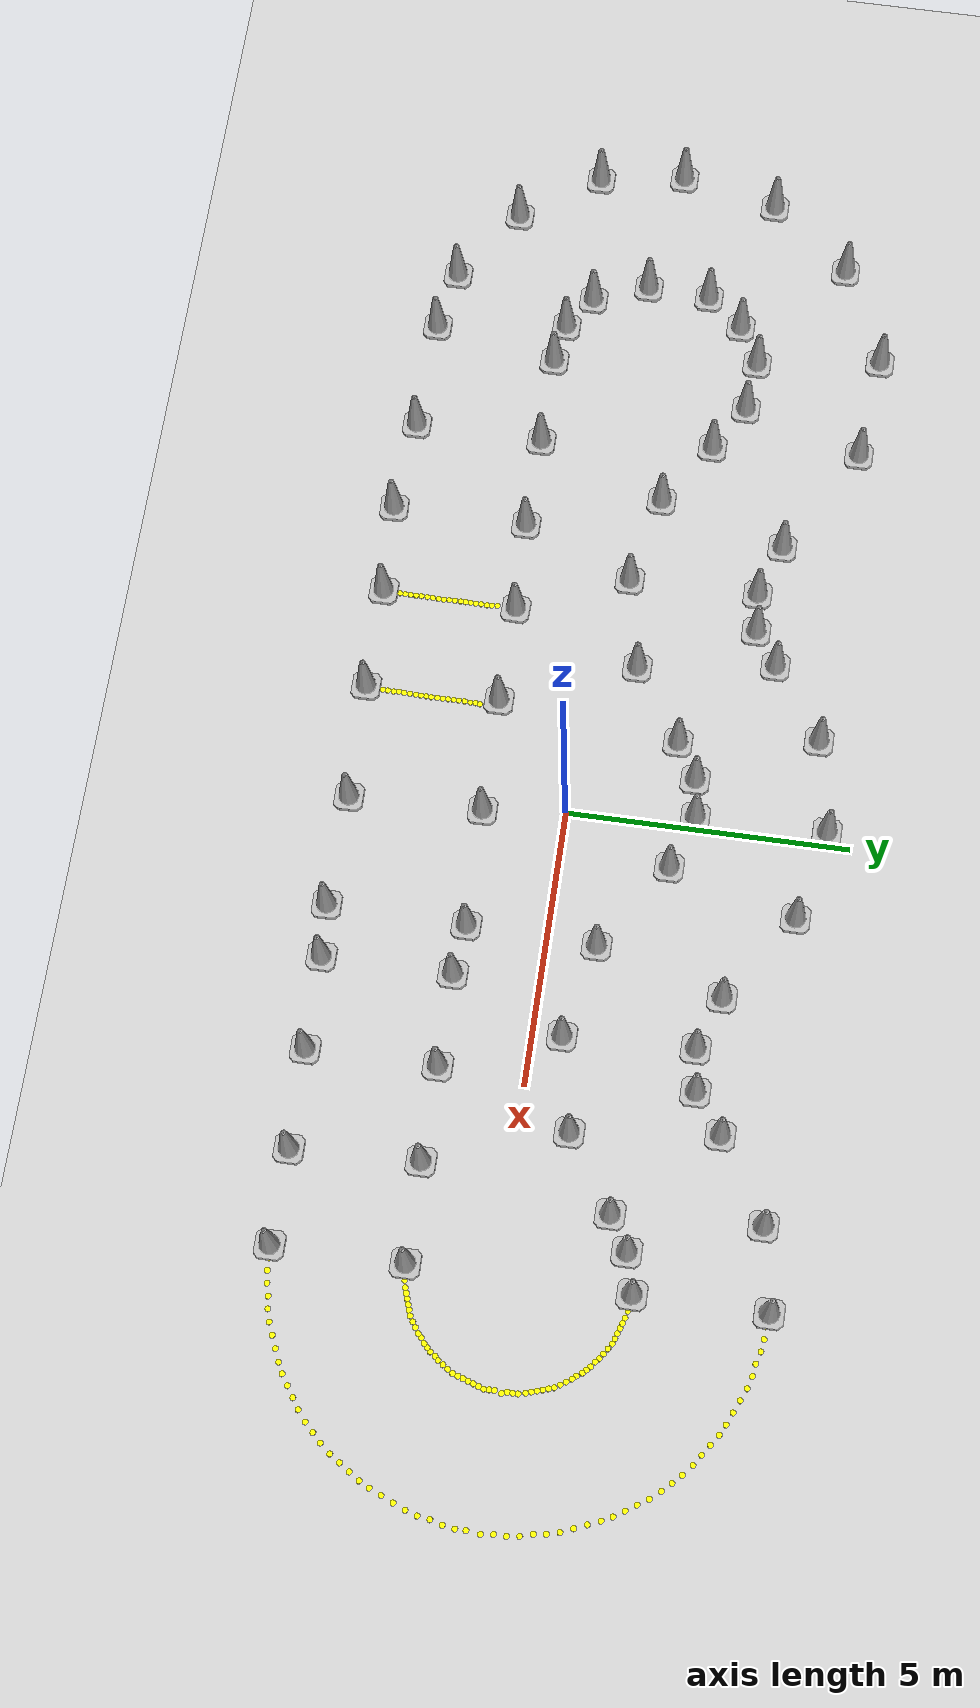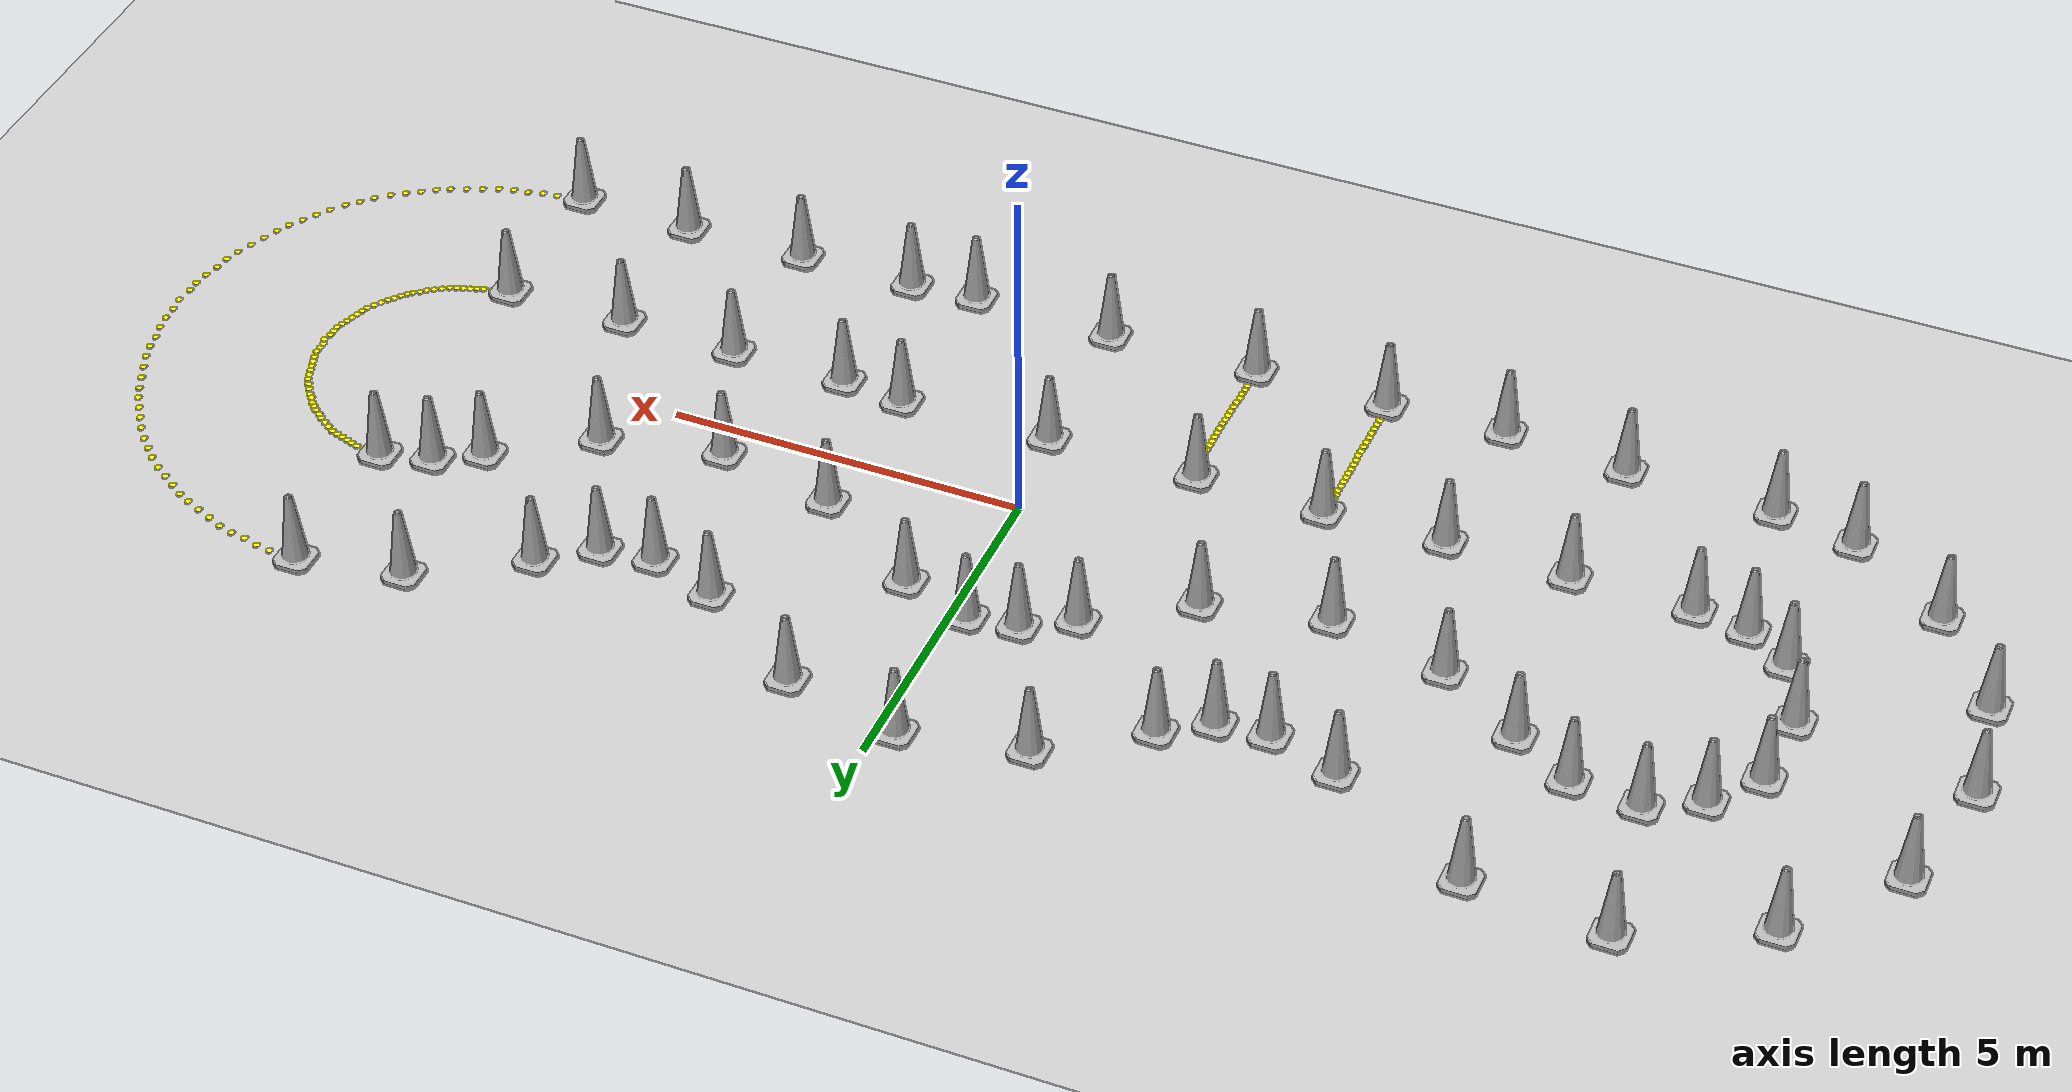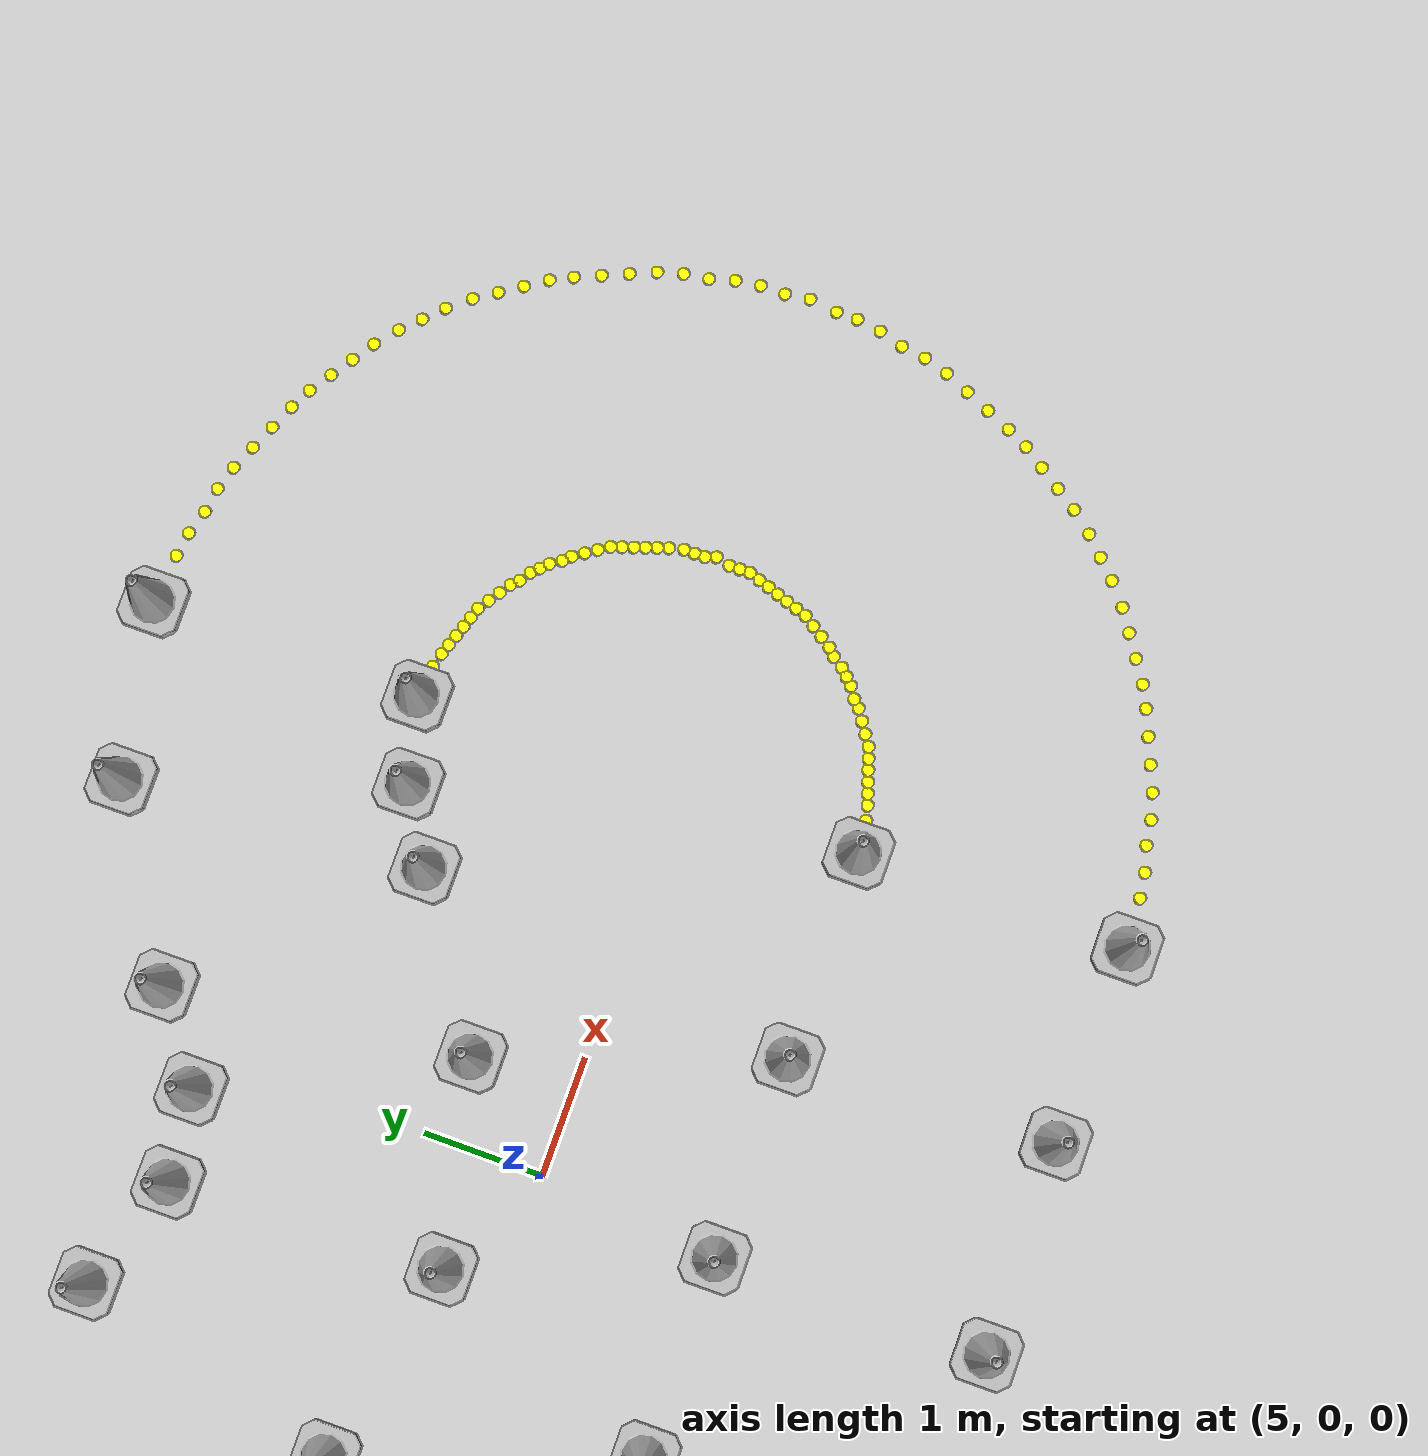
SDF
<sdf version="1.6">
 <world name="default">
  <light name="sun" type="directional">
   <pose>0 0 10 0 -0 0</pose>
   <diffuse>0.8 0.8 0.8 1</diffuse>
   <specular>0.2 0.2 0.2 1</specular>
   <attenuation>
    <range>1000</range>
    <constant>0.9</constant>
    <linear>0.01</linear>
    <quadratic>0.001</quadratic>
   </attenuation>
   <direction>-0.5 0.1 -0.9</direction>
  </light>
  <model name="ground_plane">
   <static>1</static>
   <link name="link">
    <collision name="collision">
     <geometry><plane><normal>0 0 1</normal><size>100 100</size></plane></geometry>
     <surface><friction><ode><mu>100</mu><mu2>50</mu2></ode></friction></surface>
    </collision>
    <visual name="visual">
     <cast_shadows>0</cast_shadows>
     <geometry><plane><normal>0 0 1</normal><size>100 100</size></plane></geometry>
     <material>
      <script><uri>file://media/materials/scripts/gazebo.material</uri><name>Gazebo/Grey</name></script>
     </material>
    </visual>
   </link>
  </model>
  <gravity>0 0 -9.8</gravity>
  <magnetic_field>6e-06 2.3e-05 -4.2e-05</magnetic_field>
  <atmosphere type="adiabatic"/>
  <physics name="default_physics" default="0" type="ode">
   <max_step_size>0.001</max_step_size>
   <real_time_factor>1</real_time_factor>
   <real_time_update_rate>1000</real_time_update_rate>
  </physics>
  <scene><ambient>0.4 0.4 0.4 1</ambient><background>0.7 0.7 0.7 1</background><shadows>1</shadows></scene>
  <audio><device>default</device></audio>
  <spherical_coordinates>
   <surface_model>EARTH_WGS84</surface_model>
   <latitude_deg>0</latitude_deg>
   <longitude_deg>0</longitude_deg>
   <elevation>0</elevation>
   <heading_deg>0</heading_deg>
  </spherical_coordinates>
  <model name="red_model_1">
   <link name="link">
    <collision name="collision">
     <geometry>
      <mesh><scale>10 10 10</scale><uri>model://construction_cone_red/meshes/construction_cone.dae</uri></mesh>
     </geometry>
    </collision>
    <visual name="visual">
     <geometry>
      <mesh><scale>10 10 10</scale><uri>model://construction_cone_red/meshes/construction_cone.dae</uri></mesh>
     </geometry>
    </visual>
    <inertial>
     <inertia><ixx>1</ixx><ixy>0</ixy><ixz>0</ixz><iyy>1</iyy><iyz>0</iyz><izz>1</izz></inertia>
     <mass>1</mass>
    </inertial>
   </link>
   <pose>8.27865 -1.50008 0.005 0 -0 0.000226</pose>
  </model>
  <model name="red_model_2">
   <link name="link">
    <collision name="collision">
     <geometry>
      <mesh><scale>10 10 10</scale><uri>model://construction_cone_red/meshes/construction_cone.dae</uri></mesh>
     </geometry>
    </collision>
    <visual name="visual">
     <geometry>
      <mesh><scale>10 10 10</scale><uri>model://construction_cone_red/meshes/construction_cone.dae</uri></mesh>
     </geometry>
    </visual>
    <inertial>
     <inertia><ixx>1</ixx><ixy>0</ixy><ixz>0</ixz><iyy>1</iyy><iyz>0</iyz><izz>1</izz></inertia>
     <mass>1</mass>
    </inertial>
   </link>
   <pose>4.86 -1.5 -0 0 -1e-06 0</pose>
  </model>
  <model name="red_model_3">
   <link name="link">
    <collision name="collision">
     <geometry>
      <mesh><scale>10 10 10</scale><uri>model://construction_cone_red/meshes/construction_cone.dae</uri></mesh>
     </geometry>
    </collision>
    <visual name="visual">
     <geometry>
      <mesh><scale>10 10 10</scale><uri>model://construction_cone_red/meshes/construction_cone.dae</uri></mesh>
     </geometry>
    </visual>
    <inertial>
     <inertia><ixx>1</ixx><ixy>0</ixy><ixz>0</ixz><iyy>1</iyy><iyz>0</iyz><izz>1</izz></inertia>
     <mass>1</mass>
    </inertial>
   </link>
   <pose>3.21 -1.5 -1e-05 -0 -0 -0</pose>
  </model>
  <model name="red_model_4">
   <link name="link">
    <collision name="collision">
     <geometry>
      <mesh><scale>10 10 10</scale><uri>model://construction_cone_red/meshes/construction_cone.dae</uri></mesh>
     </geometry>
    </collision>
    <visual name="visual">
     <geometry>
      <mesh><scale>10 10 10</scale><uri>model://construction_cone_red/meshes/construction_cone.dae</uri></mesh>
     </geometry>
    </visual>
    <inertial>
     <inertia><ixx>1</ixx><ixy>0</ixy><ixz>0</ixz><iyy>1</iyy><iyz>0</iyz><izz>1</izz></inertia>
     <mass>1</mass>
    </inertial>
   </link>
   <pose>2.30847 -1.40299 -0 0 -1e-06 -0.002061</pose>
  </model>
  <model name="red_model_5">
   <link name="link">
    <collision name="collision">
     <geometry>
      <mesh><scale>10 10 10</scale><uri>model://construction_cone_red/meshes/construction_cone.dae</uri></mesh>
     </geometry>
    </collision>
    <visual name="visual">
     <geometry>
      <mesh><scale>10 10 10</scale><uri>model://construction_cone_red/meshes/construction_cone.dae</uri></mesh>
     </geometry>
    </visual>
    <inertial>
     <inertia><ixx>1</ixx><ixy>0</ixy><ixz>0</ixz><iyy>1</iyy><iyz>0</iyz><izz>1</izz></inertia>
     <mass>1</mass>
    </inertial>
   </link>
   <pose>0.179842 -1.44788 -0 -0 -1e-06 0.013575</pose>
  </model>
  <model name="red_model_6">
   <link name="link">
    <collision name="collision">
     <geometry>
      <mesh><scale>10 10 10</scale><uri>model://construction_cone_red/meshes/construction_cone.dae</uri></mesh>
     </geometry>
    </collision>
    <visual name="visual">
     <geometry>
      <mesh><scale>10 10 10</scale><uri>model://construction_cone_red/meshes/construction_cone.dae</uri></mesh>
     </geometry>
    </visual>
    <inertial>
     <inertia><ixx>1</ixx><ixy>0</ixy><ixz>0</ixz><iyy>1</iyy><iyz>0</iyz><izz>1</izz></inertia>
     <mass>1</mass>
    </inertial>
   </link>
   <pose>-1.91999 -1.4699 0.005 0 -0 0.00011</pose>
  </model>
  <model name="red_model_7">
   <link name="link">
    <collision name="collision">
     <geometry>
      <mesh><scale>10 10 10</scale><uri>model://construction_cone_red/meshes/construction_cone.dae</uri></mesh>
     </geometry>
    </collision>
    <visual name="visual">
     <geometry>
      <mesh><scale>10 10 10</scale><uri>model://construction_cone_red/meshes/construction_cone.dae</uri></mesh>
     </geometry>
    </visual>
    <inertial>
     <inertia><ixx>1</ixx><ixy>0</ixy><ixz>0</ixz><iyy>1</iyy><iyz>0</iyz><izz>1</izz></inertia>
     <mass>1</mass>
    </inertial>
   </link>
   <pose>-3.71945 -1.43765 0.004995 0 0 -0.034435</pose>
  </model>
  <model name="red_model_8">
   <link name="link">
    <collision name="collision">
     <geometry>
      <mesh><scale>10 10 10</scale><uri>model://construction_cone_red/meshes/construction_cone.dae</uri></mesh>
     </geometry>
    </collision>
    <visual name="visual">
     <geometry>
      <mesh><scale>10 10 10</scale><uri>model://construction_cone_red/meshes/construction_cone.dae</uri></mesh>
     </geometry>
    </visual>
    <inertial>
     <inertia><ixx>1</ixx><ixy>0</ixy><ixz>0</ixz><iyy>1</iyy><iyz>0</iyz><izz>1</izz></inertia>
     <mass>1</mass>
    </inertial>
   </link>
   <pose>-5.4 -1.5 -0 0 -1e-06 0</pose>
  </model>
  <model name="red_model_9">
   <link name="link">
    <collision name="collision">
     <geometry>
      <mesh><scale>10 10 10</scale><uri>model://construction_cone_red/meshes/construction_cone.dae</uri></mesh>
     </geometry>
    </collision>
    <visual name="visual">
     <geometry>
      <mesh><scale>10 10 10</scale><uri>model://construction_cone_red/meshes/construction_cone.dae</uri></mesh>
     </geometry>
    </visual>
    <inertial>
     <inertia><ixx>1</ixx><ixy>0</ixy><ixz>0</ixz><iyy>1</iyy><iyz>0</iyz><izz>1</izz></inertia>
     <mass>1</mass>
    </inertial>
   </link>
   <pose>-7.11 -1.47 -0 0 -0 0</pose>
  </model>
  <model name="red_model_10">
   <link name="link">
    <collision name="collision">
     <geometry>
      <mesh><scale>10 10 10</scale><uri>model://construction_cone_red/meshes/construction_cone.dae</uri></mesh>
     </geometry>
    </collision>
    <visual name="visual">
     <geometry>
      <mesh><scale>10 10 10</scale><uri>model://construction_cone_red/meshes/construction_cone.dae</uri></mesh>
     </geometry>
    </visual>
    <inertial>
     <inertia><ixx>1</ixx><ixy>0</ixy><ixz>0</ixz><iyy>1</iyy><iyz>0</iyz><izz>1</izz></inertia>
     <mass>1</mass>
    </inertial>
   </link>
   <pose>-8.79 -1.47 -9e-06 0 -0 0</pose>
  </model>
  <model name="red_model_11">
   <link name="link">
    <collision name="collision">
     <geometry>
      <mesh><scale>10 10 10</scale><uri>model://construction_cone_red/meshes/construction_cone.dae</uri></mesh>
     </geometry>
    </collision>
    <visual name="visual">
     <geometry>
      <mesh><scale>10 10 10</scale><uri>model://construction_cone_red/meshes/construction_cone.dae</uri></mesh>
     </geometry>
    </visual>
    <inertial>
     <inertia><ixx>1</ixx><ixy>0</ixy><ixz>0</ixz><iyy>1</iyy><iyz>0</iyz><izz>1</izz></inertia>
     <mass>1</mass>
    </inertial>
   </link>
   <pose>-9.54 -1.35 -0 0 -0 0</pose>
  </model>
  <model name="red_model_12">
   <link name="link">
    <collision name="collision">
     <geometry>
      <mesh><scale>10 10 10</scale><uri>model://construction_cone_red/meshes/construction_cone.dae</uri></mesh>
     </geometry>
    </collision>
    <visual name="visual">
     <geometry>
      <mesh><scale>10 10 10</scale><uri>model://construction_cone_red/meshes/construction_cone.dae</uri></mesh>
     </geometry>
    </visual>
    <inertial>
     <inertia><ixx>1</ixx><ixy>0</ixy><ixz>0</ixz><iyy>1</iyy><iyz>0</iyz><izz>1</izz></inertia>
     <mass>1</mass>
    </inertial>
   </link>
   <pose>-10.17 -0.93 -0 0 -1e-06 0</pose>
  </model>
  <model name="red_model_13">
   <link name="link">
    <collision name="collision">
     <geometry>
      <mesh><scale>10 10 10</scale><uri>model://construction_cone_red/meshes/construction_cone.dae</uri></mesh>
     </geometry>
    </collision>
    <visual name="visual">
     <geometry>
      <mesh><scale>10 10 10</scale><uri>model://construction_cone_red/meshes/construction_cone.dae</uri></mesh>
     </geometry>
    </visual>
    <inertial>
     <inertia><ixx>1</ixx><ixy>0</ixy><ixz>0</ixz><iyy>1</iyy><iyz>0</iyz><izz>1</izz></inertia>
     <mass>1</mass>
    </inertial>
   </link>
   <pose>4.05 0.51 -1e-05 -0 -0 -0</pose>
  </model>
  <model name="red_model_14">
   <link name="link">
    <collision name="collision">
     <geometry>
      <mesh><scale>10 10 10</scale><uri>model://construction_cone_red/meshes/construction_cone.dae</uri></mesh>
     </geometry>
    </collision>
    <visual name="visual">
     <geometry>
      <mesh><scale>10 10 10</scale><uri>model://construction_cone_red/meshes/construction_cone.dae</uri></mesh>
     </geometry>
    </visual>
    <inertial>
     <inertia><ixx>1</ixx><ixy>0</ixy><ixz>0</ixz><iyy>1</iyy><iyz>0</iyz><izz>1</izz></inertia>
     <mass>1</mass>
    </inertial>
   </link>
   <pose>-10.56 0.06 -0 0 -1e-06 0</pose>
  </model>
  <model name="red_model_15">
   <link name="link">
    <collision name="collision">
     <geometry>
      <mesh><scale>10 10 10</scale><uri>model://construction_cone_red/meshes/construction_cone.dae</uri></mesh>
     </geometry>
    </collision>
    <visual name="visual">
     <geometry>
      <mesh><scale>10 10 10</scale><uri>model://construction_cone_red/meshes/construction_cone.dae</uri></mesh>
     </geometry>
    </visual>
    <inertial>
     <inertia><ixx>1</ixx><ixy>0</ixy><ixz>0</ixz><iyy>1</iyy><iyz>0</iyz><izz>1</izz></inertia>
     <mass>1</mass>
    </inertial>
   </link>
   <pose>-4.56 0.51 -0 0 -0 0</pose>
  </model>
  <model name="red_model_16">
   <link name="link">
    <collision name="collision">
     <geometry>
      <mesh><scale>10 10 10</scale><uri>model://construction_cone_red/meshes/construction_cone.dae</uri></mesh>
     </geometry>
    </collision>
    <visual name="visual">
     <geometry>
      <mesh><scale>10 10 10</scale><uri>model://construction_cone_red/meshes/construction_cone.dae</uri></mesh>
     </geometry>
    </visual>
    <inertial>
     <inertia><ixx>1</ixx><ixy>0</ixy><ixz>0</ixz><iyy>1</iyy><iyz>0</iyz><izz>1</izz></inertia>
     <mass>1</mass>
    </inertial>
   </link>
   <pose>5.7 0.87 -0 0 -0 0</pose>
  </model>
  <model name="red_model_17">
   <link name="link">
    <collision name="collision">
     <geometry>
      <mesh><scale>10 10 10</scale><uri>model://construction_cone_red/meshes/construction_cone.dae</uri></mesh>
     </geometry>
    </collision>
    <visual name="visual">
     <geometry>
      <mesh><scale>10 10 10</scale><uri>model://construction_cone_red/meshes/construction_cone.dae</uri></mesh>
     </geometry>
    </visual>
    <inertial>
     <inertia><ixx>1</ixx><ixy>0</ixy><ixz>0</ixz><iyy>1</iyy><iyz>0</iyz><izz>1</izz></inertia>
     <mass>1</mass>
    </inertial>
   </link>
   <pose>2.37 0.87 -0 0 -0 0</pose>
  </model>
  <model name="red_model_18">
   <link name="link">
    <collision name="collision">
     <geometry>
      <mesh><scale>10 10 10</scale><uri>model://construction_cone_red/meshes/construction_cone.dae</uri></mesh>
     </geometry>
    </collision>
    <visual name="visual">
     <geometry>
      <mesh><scale>10 10 10</scale><uri>model://construction_cone_red/meshes/construction_cone.dae</uri></mesh>
     </geometry>
    </visual>
    <inertial>
     <inertia><ixx>1</ixx><ixy>0</ixy><ixz>0</ixz><iyy>1</iyy><iyz>0</iyz><izz>1</izz></inertia>
     <mass>1</mass>
    </inertial>
   </link>
   <pose>-2.88 0.87 -0 0 -1e-06 0</pose>
  </model>
  <model name="red_model_19">
   <link name="link">
    <collision name="collision">
     <geometry>
      <mesh><scale>10 10 10</scale><uri>model://construction_cone_red/meshes/construction_cone.dae</uri></mesh>
     </geometry>
    </collision>
    <visual name="visual">
     <geometry>
      <mesh><scale>10 10 10</scale><uri>model://construction_cone_red/meshes/construction_cone.dae</uri></mesh>
     </geometry>
    </visual>
    <inertial>
     <inertia><ixx>1</ixx><ixy>0</ixy><ixz>0</ixz><iyy>1</iyy><iyz>0</iyz><izz>1</izz></inertia>
     <mass>1</mass>
    </inertial>
   </link>
   <pose>-6.21 0.87 -0 0 -0 0</pose>
  </model>
  <model name="red_model_20">
   <link name="link">
    <collision name="collision">
     <geometry>
      <mesh><scale>10 10 10</scale><uri>model://construction_cone_red/meshes/construction_cone.dae</uri></mesh>
     </geometry>
    </collision>
    <visual name="visual">
     <geometry>
      <mesh><scale>10 10 10</scale><uri>model://construction_cone_red/meshes/construction_cone.dae</uri></mesh>
     </geometry>
    </visual>
    <inertial>
     <inertia><ixx>1</ixx><ixy>0</ixy><ixz>0</ixz><iyy>1</iyy><iyz>0</iyz><izz>1</izz></inertia>
     <mass>1</mass>
    </inertial>
   </link>
   <pose>-10.5 1.2 -0 0 -0 0</pose>
  </model>
  <model name="red_model_21">
   <link name="link">
    <collision name="collision">
     <geometry>
      <mesh><scale>10 10 10</scale><uri>model://construction_cone_red/meshes/construction_cone.dae</uri></mesh>
     </geometry>
    </collision>
    <visual name="visual">
     <geometry>
      <mesh><scale>10 10 10</scale><uri>model://construction_cone_red/meshes/construction_cone.dae</uri></mesh>
     </geometry>
    </visual>
    <inertial>
     <inertia><ixx>1</ixx><ixy>0</ixy><ixz>0</ixz><iyy>1</iyy><iyz>0</iyz><izz>1</izz></inertia>
     <mass>1</mass>
    </inertial>
   </link>
   <pose>-1.56 1.77 -0 0 -0 0</pose>
  </model>
  <model name="red_model_22">
   <link name="link">
    <collision name="collision">
     <geometry>
      <mesh><scale>10 10 10</scale><uri>model://construction_cone_red/meshes/construction_cone.dae</uri></mesh>
     </geometry>
    </collision>
    <visual name="visual">
     <geometry>
      <mesh><scale>10 10 10</scale><uri>model://construction_cone_red/meshes/construction_cone.dae</uri></mesh>
     </geometry>
    </visual>
    <inertial>
     <inertia><ixx>1</ixx><ixy>0</ixy><ixz>0</ixz><iyy>1</iyy><iyz>0</iyz><izz>1</izz></inertia>
     <mass>1</mass>
    </inertial>
   </link>
   <pose>-7.41 1.65 -0 0 -1e-06 0</pose>
  </model>
  <model name="red_model_23">
   <link name="link">
    <collision name="collision">
     <geometry>
      <mesh><scale>10 10 10</scale><uri>model://construction_cone_red/meshes/construction_cone.dae</uri></mesh>
     </geometry>
    </collision>
    <visual name="visual">
     <geometry>
      <mesh><scale>10 10 10</scale><uri>model://construction_cone_red/meshes/construction_cone.dae</uri></mesh>
     </geometry>
    </visual>
    <inertial>
     <inertia><ixx>1</ixx><ixy>0</ixy><ixz>0</ixz><iyy>1</iyy><iyz>0</iyz><izz>1</izz></inertia>
     <mass>1</mass>
    </inertial>
   </link>
   <pose>6.99 1.74 0 -0 -0 -0</pose>
  </model>
  <model name="red_model_24">
   <link name="link">
    <collision name="collision">
     <geometry>
      <mesh><scale>10 10 10</scale><uri>model://construction_cone_red/meshes/construction_cone.dae</uri></mesh>
     </geometry>
    </collision>
    <visual name="visual">
     <geometry>
      <mesh><scale>10 10 10</scale><uri>model://construction_cone_red/meshes/construction_cone.dae</uri></mesh>
     </geometry>
    </visual>
    <inertial>
     <inertia><ixx>1</ixx><ixy>0</ixy><ixz>0</ixz><iyy>1</iyy><iyz>0</iyz><izz>1</izz></inertia>
     <mass>1</mass>
    </inertial>
   </link>
   <pose>-9.96 1.86 -0 0 -1e-06 0</pose>
  </model>
  <model name="red_model_25">
   <link name="link">
    <collision name="collision">
     <geometry>
      <mesh><scale>10 10 10</scale><uri>model://construction_cone_red/meshes/construction_cone.dae</uri></mesh>
     </geometry>
    </collision>
    <visual name="visual">
     <geometry>
      <mesh><scale>10 10 10</scale><uri>model://construction_cone_red/meshes/construction_cone.dae</uri></mesh>
     </geometry>
    </visual>
    <inertial>
     <inertia><ixx>1</ixx><ixy>0</ixy><ixz>0</ixz><iyy>1</iyy><iyz>0</iyz><izz>1</izz></inertia>
     <mass>1</mass>
    </inertial>
   </link>
   <pose>0.78 1.92 -0 0 -0 0</pose>
  </model>
  <model name="red_model_26">
   <link name="link">
    <collision name="collision">
     <geometry>
      <mesh><scale>10 10 10</scale><uri>model://construction_cone_red/meshes/construction_cone.dae</uri></mesh>
     </geometry>
    </collision>
    <visual name="visual">
     <geometry>
      <mesh><scale>10 10 10</scale><uri>model://construction_cone_red/meshes/construction_cone.dae</uri></mesh>
     </geometry>
    </visual>
    <inertial>
     <inertia><ixx>1</ixx><ixy>0</ixy><ixz>0</ixz><iyy>1</iyy><iyz>0</iyz><izz>1</izz></inertia>
     <mass>1</mass>
    </inertial>
   </link>
   <pose>-0.9 2.16 -0 0 -0 0</pose>
  </model>
  <model name="red_model_27">
   <link name="link">
    <collision name="collision">
     <geometry>
      <mesh><scale>10 10 10</scale><uri>model://construction_cone_red/meshes/construction_cone.dae</uri></mesh>
     </geometry>
    </collision>
    <visual name="visual">
     <geometry>
      <mesh><scale>10 10 10</scale><uri>model://construction_cone_red/meshes/construction_cone.dae</uri></mesh>
     </geometry>
    </visual>
    <inertial>
     <inertia><ixx>1</ixx><ixy>0</ixy><ixz>0</ixz><iyy>1</iyy><iyz>0</iyz><izz>1</izz></inertia>
     <mass>1</mass>
    </inertial>
   </link>
   <pose>7.58615 2.09928 0.002805 0.000936 -0.010521 0.005874</pose>
  </model>
  <model name="red_model_28">
   <link name="link">
    <collision name="collision">
     <geometry>
      <mesh><scale>10 10 10</scale><uri>model://construction_cone_red/meshes/construction_cone.dae</uri></mesh>
     </geometry>
    </collision>
    <visual name="visual">
     <geometry>
      <mesh><scale>10 10 10</scale><uri>model://construction_cone_red/meshes/construction_cone.dae</uri></mesh>
     </geometry>
    </visual>
    <inertial>
     <inertia><ixx>1</ixx><ixy>0</ixy><ixz>0</ixz><iyy>1</iyy><iyz>0</iyz><izz>1</izz></inertia>
     <mass>1</mass>
    </inertial>
   </link>
   <pose>-8.28 2.16 -0 0 -1e-06 0</pose>
  </model>
  <model name="red_model_29">
   <link name="link">
    <collision name="collision">
     <geometry>
      <mesh><scale>10 10 10</scale><uri>model://construction_cone_red/meshes/construction_cone.dae</uri></mesh>
     </geometry>
    </collision>
    <visual name="visual">
     <geometry>
      <mesh><scale>10 10 10</scale><uri>model://construction_cone_red/meshes/construction_cone.dae</uri></mesh>
     </geometry>
    </visual>
    <inertial>
     <inertia><ixx>1</ixx><ixy>0</ixy><ixz>0</ixz><iyy>1</iyy><iyz>0</iyz><izz>1</izz></inertia>
     <mass>1</mass>
    </inertial>
   </link>
   <pose>-9.24 2.25 -0 0 -0 0</pose>
  </model>
  <model name="red_model_30">
   <link name="link">
    <collision name="collision">
     <geometry>
      <mesh><scale>10 10 10</scale><uri>model://construction_cone_red/meshes/construction_cone.dae</uri></mesh>
     </geometry>
    </collision>
    <visual name="visual">
     <geometry>
      <mesh><scale>10 10 10</scale><uri>model://construction_cone_red/meshes/construction_cone.dae</uri></mesh>
     </geometry>
    </visual>
    <inertial>
     <inertia><ixx>1</ixx><ixy>0</ixy><ixz>0</ixz><iyy>1</iyy><iyz>0</iyz><izz>1</izz></inertia>
     <mass>1</mass>
    </inertial>
   </link>
   <pose>8.28 2.28001 0.005 -1e-06 -0 3e-06</pose>
  </model>
  <model name="red_model_31">
   <link name="link">
    <collision name="collision">
     <geometry>
      <mesh><scale>10 10 10</scale><uri>model://construction_cone_red/meshes/construction_cone.dae</uri></mesh>
     </geometry>
    </collision>
    <visual name="visual">
     <geometry>
      <mesh><scale>10 10 10</scale><uri>model://construction_cone_red/meshes/construction_cone.dae</uri></mesh>
     </geometry>
    </visual>
    <inertial>
     <inertia><ixx>1</ixx><ixy>0</ixy><ixz>0</ixz><iyy>1</iyy><iyz>0</iyz><izz>1</izz></inertia>
     <mass>1</mass>
    </inertial>
   </link>
   <pose>-0.21 2.25 -0 0 -1e-06 0</pose>
  </model>
  <model name="blue_model_0">
   <link name="link">
    <collision name="collision">
     <geometry>
      <mesh><scale>10 10 10</scale><uri>model://construction_cone_blue/meshes/construction_cone.dae</uri></mesh>
     </geometry>
    </collision>
    <visual name="visual">
     <geometry>
      <mesh><scale>10 10 10</scale><uri>model://construction_cone_blue/meshes/construction_cone.dae</uri></mesh>
     </geometry>
    </visual>
    <inertial>
     <inertia><ixx>1</ixx><ixy>0</ixy><ixz>0</ixz><iyy>1</iyy><iyz>0</iyz><izz>1</izz></inertia>
     <mass>1</mass>
    </inertial>
   </link>
   <pose>2.26467 -3.84976 -8e-06 1e-06 -0 0.01861</pose>
  </model>
  <model name="blue_model_1">
   <link name="link">
    <collision name="collision">
     <geometry>
      <mesh><scale>10 10 10</scale><uri>model://construction_cone_blue/meshes/construction_cone.dae</uri></mesh>
     </geometry>
    </collision>
    <visual name="visual">
     <geometry>
      <mesh><scale>10 10 10</scale><uri>model://construction_cone_blue/meshes/construction_cone.dae</uri></mesh>
     </geometry>
    </visual>
    <inertial>
     <inertia><ixx>1</ixx><ixy>0</ixy><ixz>0</ixz><iyy>1</iyy><iyz>0</iyz><izz>1</izz></inertia>
     <mass>1</mass>
    </inertial>
   </link>
   <pose>0.245736 -3.79958 -0 0 -1e-06 0.018627</pose>
  </model>
  <model name="blue_model_2">
   <link name="link">
    <collision name="collision">
     <geometry>
      <mesh><scale>10 10 10</scale><uri>model://construction_cone_blue/meshes/construction_cone.dae</uri></mesh>
     </geometry>
    </collision>
    <visual name="visual">
     <geometry>
      <mesh><scale>10 10 10</scale><uri>model://construction_cone_blue/meshes/construction_cone.dae</uri></mesh>
     </geometry>
    </visual>
    <inertial>
     <inertia><ixx>1</ixx><ixy>0</ixy><ixz>0</ixz><iyy>1</iyy><iyz>0</iyz><izz>1</izz></inertia>
     <mass>1</mass>
    </inertial>
   </link>
   <pose>-3.74995 -3.84019 0.004992 -0 -1e-06 -0.00015</pose>
  </model>
  <model name="blue_model_3">
   <link name="link">
    <collision name="collision">
     <geometry>
      <mesh><scale>10 10 10</scale><uri>model://construction_cone_blue/meshes/construction_cone.dae</uri></mesh>
     </geometry>
    </collision>
    <visual name="visual">
     <geometry>
      <mesh><scale>10 10 10</scale><uri>model://construction_cone_blue/meshes/construction_cone.dae</uri></mesh>
     </geometry>
    </visual>
    <inertial>
     <inertia><ixx>1</ixx><ixy>0</ixy><ixz>0</ixz><iyy>1</iyy><iyz>0</iyz><izz>1</izz></inertia>
     <mass>1</mass>
    </inertial>
   </link>
   <pose>8.28 -3.78 0.004998 0 -0 0</pose>
  </model>
  <model name="blue_model_4">
   <link name="link">
    <collision name="collision">
     <geometry>
      <mesh><scale>10 10 10</scale><uri>model://construction_cone_blue/meshes/construction_cone.dae</uri></mesh>
     </geometry>
    </collision>
    <visual name="visual">
     <geometry>
      <mesh><scale>10 10 10</scale><uri>model://construction_cone_blue/meshes/construction_cone.dae</uri></mesh>
     </geometry>
    </visual>
    <inertial>
     <inertia><ixx>1</ixx><ixy>0</ixy><ixz>0</ixz><iyy>1</iyy><iyz>0</iyz><izz>1</izz></inertia>
     <mass>1</mass>
    </inertial>
   </link>
   <pose>3.21 -3.78 -1e-05 0 -0 0</pose>
  </model>
  <model name="blue_model_5">
   <link name="link">
    <collision name="collision">
     <geometry>
      <mesh><scale>10 10 10</scale><uri>model://construction_cone_blue/meshes/construction_cone.dae</uri></mesh>
     </geometry>
    </collision>
    <visual name="visual">
     <geometry>
      <mesh><scale>10 10 10</scale><uri>model://construction_cone_blue/meshes/construction_cone.dae</uri></mesh>
     </geometry>
    </visual>
    <inertial>
     <inertia><ixx>1</ixx><ixy>0</ixy><ixz>0</ixz><iyy>1</iyy><iyz>0</iyz><izz>1</izz></inertia>
     <mass>1</mass>
    </inertial>
   </link>
   <pose>-5.41428 -3.92101 -0 0 -1e-06 -3.10196</pose>
  </model>
  <model name="blue_model_6">
   <link name="link">
    <collision name="collision">
     <geometry>
      <mesh><scale>10 10 10</scale><uri>model://construction_cone_blue/meshes/construction_cone.dae</uri></mesh>
     </geometry>
    </collision>
    <visual name="visual">
     <geometry>
      <mesh><scale>10 10 10</scale><uri>model://construction_cone_blue/meshes/construction_cone.dae</uri></mesh>
     </geometry>
    </visual>
    <inertial>
     <inertia><ixx>1</ixx><ixy>0</ixy><ixz>0</ixz><iyy>1</iyy><iyz>0</iyz><izz>1</izz></inertia>
     <mass>1</mass>
    </inertial>
   </link>
   <pose>-7.14 -3.78 -0 0 -1e-06 0</pose>
  </model>
  <model name="blue_model_7">
   <link name="link">
    <collision name="collision">
     <geometry>
      <mesh><scale>10 10 10</scale><uri>model://construction_cone_blue/meshes/construction_cone.dae</uri></mesh>
     </geometry>
    </collision>
    <visual name="visual">
     <geometry>
      <mesh><scale>10 10 10</scale><uri>model://construction_cone_blue/meshes/construction_cone.dae</uri></mesh>
     </geometry>
    </visual>
    <inertial>
     <inertia><ixx>1</ixx><ixy>0</ixy><ixz>0</ixz><iyy>1</iyy><iyz>0</iyz><izz>1</izz></inertia>
     <mass>1</mass>
    </inertial>
   </link>
   <pose>-9.21 -3.72 -0 0 -1e-06 0</pose>
  </model>
  <model name="blue_model_8">
   <link name="link">
    <collision name="collision">
     <geometry>
      <mesh><scale>10 10 10</scale><uri>model://construction_cone_blue/meshes/construction_cone.dae</uri></mesh>
     </geometry>
    </collision>
    <visual name="visual">
     <geometry>
      <mesh><scale>10 10 10</scale><uri>model://construction_cone_blue/meshes/construction_cone.dae</uri></mesh>
     </geometry>
    </visual>
    <inertial>
     <inertia><ixx>1</ixx><ixy>0</ixy><ixz>0</ixz><iyy>1</iyy><iyz>0</iyz><izz>1</izz></inertia>
     <mass>1</mass>
    </inertial>
   </link>
   <pose>-10.35 -3.51 -0 0 -1e-06 0</pose>
  </model>
  <model name="blue_model_11">
   <link name="link">
    <collision name="collision">
     <geometry>
      <mesh><scale>10 10 10</scale><uri>model://construction_cone_blue/meshes/construction_cone.dae</uri></mesh>
     </geometry>
    </collision>
    <visual name="visual">
     <geometry>
      <mesh><scale>10 10 10</scale><uri>model://construction_cone_blue/meshes/construction_cone.dae</uri></mesh>
     </geometry>
    </visual>
    <inertial>
     <inertia><ixx>1</ixx><ixy>0</ixy><ixz>0</ixz><iyy>1</iyy><iyz>0</iyz><izz>1</izz></inertia>
     <mass>1</mass>
    </inertial>
   </link>
   <pose>-11.76 -2.55 -0 0 -1e-06 0</pose>
  </model>
  <model name="blue_model_13">
   <link name="link">
    <collision name="collision">
     <geometry>
      <mesh><scale>10 10 10</scale><uri>model://construction_cone_blue/meshes/construction_cone.dae</uri></mesh>
     </geometry>
    </collision>
    <visual name="visual">
     <geometry>
      <mesh><scale>10 10 10</scale><uri>model://construction_cone_blue/meshes/construction_cone.dae</uri></mesh>
     </geometry>
    </visual>
    <inertial>
     <inertia><ixx>1</ixx><ixy>0</ixy><ixz>0</ixz><iyy>1</iyy><iyz>0</iyz><izz>1</izz></inertia>
     <mass>1</mass>
    </inertial>
   </link>
   <pose>-12.75 -1.14 -0 0 -0 0</pose>
  </model>
  <model name="blue_model_14">
   <link name="link">
    <collision name="collision">
     <geometry>
      <mesh><scale>10 10 10</scale><uri>model://construction_cone_blue/meshes/construction_cone.dae</uri></mesh>
     </geometry>
    </collision>
    <visual name="visual">
     <geometry>
      <mesh><scale>10 10 10</scale><uri>model://construction_cone_blue/meshes/construction_cone.dae</uri></mesh>
     </geometry>
    </visual>
    <inertial>
     <inertia><ixx>1</ixx><ixy>0</ixy><ixz>0</ixz><iyy>1</iyy><iyz>0</iyz><izz>1</izz></inertia>
     <mass>1</mass>
    </inertial>
   </link>
   <pose>-12.99 0.42 -0 0 -1e-06 0</pose>
  </model>
  <model name="blue_model_15">
   <link name="link">
    <collision name="collision">
     <geometry>
      <mesh><scale>10 10 10</scale><uri>model://construction_cone_blue/meshes/construction_cone.dae</uri></mesh>
     </geometry>
    </collision>
    <visual name="visual">
     <geometry>
      <mesh><scale>10 10 10</scale><uri>model://construction_cone_blue/meshes/construction_cone.dae</uri></mesh>
     </geometry>
    </visual>
    <inertial>
     <inertia><ixx>1</ixx><ixy>0</ixy><ixz>0</ixz><iyy>1</iyy><iyz>0</iyz><izz>1</izz></inertia>
     <mass>1</mass>
    </inertial>
   </link>
   <pose>-12.6 2.19 -0 0 -1e-06 0</pose>
  </model>
  <model name="blue_model_16">
   <link name="link">
    <collision name="collision">
     <geometry>
      <mesh><scale>10 10 10</scale><uri>model://construction_cone_blue/meshes/construction_cone.dae</uri></mesh>
     </geometry>
    </collision>
    <visual name="visual">
     <geometry>
      <mesh><scale>10 10 10</scale><uri>model://construction_cone_blue/meshes/construction_cone.dae</uri></mesh>
     </geometry>
    </visual>
    <inertial>
     <inertia><ixx>1</ixx><ixy>0</ixy><ixz>0</ixz><iyy>1</iyy><iyz>0</iyz><izz>1</izz></inertia>
     <mass>1</mass>
    </inertial>
   </link>
   <pose>3.96 2.79 -0 0 -1e-06 0</pose>
  </model>
  <model name="blue_model_17">
   <link name="link">
    <collision name="collision">
     <geometry>
      <mesh><scale>10 10 10</scale><uri>model://construction_cone_blue/meshes/construction_cone.dae</uri></mesh>
     </geometry>
    </collision>
    <visual name="visual">
     <geometry>
      <mesh><scale>10 10 10</scale><uri>model://construction_cone_blue/meshes/construction_cone.dae</uri></mesh>
     </geometry>
    </visual>
    <inertial>
     <inertia><ixx>1</ixx><ixy>0</ixy><ixz>0</ixz><iyy>1</iyy><iyz>0</iyz><izz>1</izz></inertia>
     <mass>1</mass>
    </inertial>
   </link>
   <pose>-4.59 2.82 -0 0 -0 0</pose>
  </model>
  <model name="blue_model_18">
   <link name="link">
    <collision name="collision">
     <geometry>
      <mesh><scale>10 10 10</scale><uri>model://construction_cone_blue/meshes/construction_cone.dae</uri></mesh>
     </geometry>
    </collision>
    <visual name="visual">
     <geometry>
      <mesh><scale>10 10 10</scale><uri>model://construction_cone_blue/meshes/construction_cone.dae</uri></mesh>
     </geometry>
    </visual>
    <inertial>
     <inertia><ixx>1</ixx><ixy>0</ixy><ixz>0</ixz><iyy>1</iyy><iyz>0</iyz><izz>1</izz></inertia>
     <mass>1</mass>
    </inertial>
   </link>
   <pose>4.71 2.88 -8e-06 1e-06 -0 0</pose>
  </model>
  <model name="blue_model_19">
   <link name="link">
    <collision name="collision">
     <geometry>
      <mesh><scale>10 10 10</scale><uri>model://construction_cone_blue/meshes/construction_cone.dae</uri></mesh>
     </geometry>
    </collision>
    <visual name="visual">
     <geometry>
      <mesh><scale>10 10 10</scale><uri>model://construction_cone_blue/meshes/construction_cone.dae</uri></mesh>
     </geometry>
    </visual>
    <inertial>
     <inertia><ixx>1</ixx><ixy>0</ixy><ixz>0</ixz><iyy>1</iyy><iyz>0</iyz><izz>1</izz></inertia>
     <mass>1</mass>
    </inertial>
   </link>
   <pose>-3.87 2.88 -0 0 -1e-06 0</pose>
  </model>
  <model name="blue_model_20">
   <link name="link">
    <collision name="collision">
     <geometry>
      <mesh><scale>10 10 10</scale><uri>model://construction_cone_blue/meshes/construction_cone.dae</uri></mesh>
     </geometry>
    </collision>
    <visual name="visual">
     <geometry>
      <mesh><scale>10 10 10</scale><uri>model://construction_cone_blue/meshes/construction_cone.dae</uri></mesh>
     </geometry>
    </visual>
    <inertial>
     <inertia><ixx>1</ixx><ixy>0</ixy><ixz>0</ixz><iyy>1</iyy><iyz>0</iyz><izz>1</izz></inertia>
     <mass>1</mass>
    </inertial>
   </link>
   <pose>3 3.12 -1e-05 0 -0 0</pose>
  </model>
  <model name="blue_model_21">
   <link name="link">
    <collision name="collision">
     <geometry>
      <mesh><scale>10 10 10</scale><uri>model://construction_cone_blue/meshes/construction_cone.dae</uri></mesh>
     </geometry>
    </collision>
    <visual name="visual">
     <geometry>
      <mesh><scale>10 10 10</scale><uri>model://construction_cone_blue/meshes/construction_cone.dae</uri></mesh>
     </geometry>
    </visual>
    <inertial>
     <inertia><ixx>1</ixx><ixy>0</ixy><ixz>0</ixz><iyy>1</iyy><iyz>0</iyz><izz>1</izz></inertia>
     <mass>1</mass>
    </inertial>
   </link>
   <pose>-3.24 3.3 -0 0 -1e-06 0</pose>
  </model>
  <model name="blue_model_22">
   <link name="link">
    <collision name="collision">
     <geometry>
      <mesh><scale>10 10 10</scale><uri>model://construction_cone_blue/meshes/construction_cone.dae</uri></mesh>
     </geometry>
    </collision>
    <visual name="visual">
     <geometry>
      <mesh><scale>10 10 10</scale><uri>model://construction_cone_blue/meshes/construction_cone.dae</uri></mesh>
     </geometry>
    </visual>
    <inertial>
     <inertia><ixx>1</ixx><ixy>0</ixy><ixz>0</ixz><iyy>1</iyy><iyz>0</iyz><izz>1</izz></inertia>
     <mass>1</mass>
    </inertial>
   </link>
   <pose>-5.58 3.15 -0 0 -0 0</pose>
  </model>
  <model name="blue_model_23">
   <link name="link">
    <collision name="collision">
     <geometry>
      <mesh><scale>10 10 10</scale><uri>model://construction_cone_blue/meshes/construction_cone.dae</uri></mesh>
     </geometry>
    </collision>
    <visual name="visual">
     <geometry>
      <mesh><scale>10 10 10</scale><uri>model://construction_cone_blue/meshes/construction_cone.dae</uri></mesh>
     </geometry>
    </visual>
    <inertial>
     <inertia><ixx>1</ixx><ixy>0</ixy><ixz>0</ixz><iyy>1</iyy><iyz>0</iyz><izz>1</izz></inertia>
     <mass>1</mass>
    </inertial>
   </link>
   <pose>5.4 3.39 -0 0 -0 0</pose>
  </model>
  <model name="blue_model_24">
   <link name="link">
    <collision name="collision">
     <geometry>
      <mesh><scale>10 10 10</scale><uri>model://construction_cone_blue/meshes/construction_cone.dae</uri></mesh>
     </geometry>
    </collision>
    <visual name="visual">
     <geometry>
      <mesh><scale>10 10 10</scale><uri>model://construction_cone_blue/meshes/construction_cone.dae</uri></mesh>
     </geometry>
    </visual>
    <inertial>
     <inertia><ixx>1</ixx><ixy>0</ixy><ixz>0</ixz><iyy>1</iyy><iyz>0</iyz><izz>1</izz></inertia>
     <mass>1</mass>
    </inertial>
   </link>
   <pose>-11.4 3.66 -0 0 -1e-06 0</pose>
  </model>
  <model name="blue_model_25">
   <link name="link">
    <collision name="collision">
     <geometry>
      <mesh><scale>10 10 10</scale><uri>model://construction_cone_blue/meshes/construction_cone.dae</uri></mesh>
     </geometry>
    </collision>
    <visual name="visual">
     <geometry>
      <mesh><scale>10 10 10</scale><uri>model://construction_cone_blue/meshes/construction_cone.dae</uri></mesh>
     </geometry>
    </visual>
    <inertial>
     <inertia><ixx>1</ixx><ixy>0</ixy><ixz>0</ixz><iyy>1</iyy><iyz>0</iyz><izz>1</izz></inertia>
     <mass>1</mass>
    </inertial>
   </link>
   <pose>1.41 4.2 -1e-05 -0 -0 -0</pose>
  </model>
  <model name="blue_model_26">
   <link name="link">
    <collision name="collision">
     <geometry>
      <mesh><scale>10 10 10</scale><uri>model://construction_cone_blue/meshes/construction_cone.dae</uri></mesh>
     </geometry>
    </collision>
    <visual name="visual">
     <geometry>
      <mesh><scale>10 10 10</scale><uri>model://construction_cone_blue/meshes/construction_cone.dae</uri></mesh>
     </geometry>
    </visual>
    <inertial>
     <inertia><ixx>1</ixx><ixy>0</ixy><ixz>0</ixz><iyy>1</iyy><iyz>0</iyz><izz>1</izz></inertia>
     <mass>1</mass>
    </inertial>
   </link>
   <pose>-1.92 4.23 -0 0 -0 0</pose>
  </model>
  <model name="blue_model_27">
   <link name="link">
    <collision name="collision">
     <geometry>
      <mesh><scale>10 10 10</scale><uri>model://construction_cone_blue/meshes/construction_cone.dae</uri></mesh>
     </geometry>
    </collision>
    <visual name="visual">
     <geometry>
      <mesh><scale>10 10 10</scale><uri>model://construction_cone_blue/meshes/construction_cone.dae</uri></mesh>
     </geometry>
    </visual>
    <inertial>
     <inertia><ixx>1</ixx><ixy>0</ixy><ixz>0</ixz><iyy>1</iyy><iyz>0</iyz><izz>1</izz></inertia>
     <mass>1</mass>
    </inertial>
   </link>
   <pose>6.84 4.29 -0 0 -1e-06 0</pose>
  </model>
  <model name="blue_model_28">
   <link name="link">
    <collision name="collision">
     <geometry>
      <mesh><scale>10 10 10</scale><uri>model://construction_cone_blue/meshes/construction_cone.dae</uri></mesh>
     </geometry>
    </collision>
    <visual name="visual">
     <geometry>
      <mesh><scale>10 10 10</scale><uri>model://construction_cone_blue/meshes/construction_cone.dae</uri></mesh>
     </geometry>
    </visual>
    <inertial>
     <inertia><ixx>1</ixx><ixy>0</ixy><ixz>0</ixz><iyy>1</iyy><iyz>0</iyz><izz>1</izz></inertia>
     <mass>1</mass>
    </inertial>
   </link>
   <pose>-7.62 4.32 -0 0 -1e-06 0</pose>
  </model>
  <model name="blue_model_29">
   <link name="link">
    <collision name="collision">
     <geometry>
      <mesh><scale>10 10 10</scale><uri>model://construction_cone_blue/meshes/construction_cone.dae</uri></mesh>
     </geometry>
    </collision>
    <visual name="visual">
     <geometry>
      <mesh><scale>10 10 10</scale><uri>model://construction_cone_blue/meshes/construction_cone.dae</uri></mesh>
     </geometry>
    </visual>
    <inertial>
     <inertia><ixx>1</ixx><ixy>0</ixy><ixz>0</ixz><iyy>1</iyy><iyz>0</iyz><izz>1</izz></inertia>
     <mass>1</mass>
    </inertial>
   </link>
   <pose>-9.57 4.5 -0 0 -0 0</pose>
  </model>
  <model name="blue_model_30">
   <link name="link">
    <collision name="collision">
     <geometry>
      <mesh><scale>10 10 10</scale><uri>model://construction_cone_blue/meshes/construction_cone.dae</uri></mesh>
     </geometry>
    </collision>
    <visual name="visual">
     <geometry>
      <mesh><scale>10 10 10</scale><uri>model://construction_cone_blue/meshes/construction_cone.dae</uri></mesh>
     </geometry>
    </visual>
    <inertial>
     <inertia><ixx>1</ixx><ixy>0</ixy><ixz>0</ixz><iyy>1</iyy><iyz>0</iyz><izz>1</izz></inertia>
     <mass>1</mass>
    </inertial>
   </link>
   <pose>8.28 4.56 0.005 -0 -0 -0</pose>
  </model>
  <model name="blue_model_31">
   <link name="link">
    <collision name="collision">
     <geometry>
      <mesh><scale>10 10 10</scale><uri>model://construction_cone_blue/meshes/construction_cone.dae</uri></mesh>
     </geometry>
    </collision>
    <visual name="visual">
     <geometry>
      <mesh><scale>10 10 10</scale><uri>model://construction_cone_blue/meshes/construction_cone.dae</uri></mesh>
     </geometry>
    </visual>
    <inertial>
     <inertia><ixx>1</ixx><ixy>0</ixy><ixz>0</ixz><iyy>1</iyy><iyz>0</iyz><izz>1</izz></inertia>
     <mass>1</mass>
    </inertial>
   </link>
   <pose>-0.24 4.56 -0 0 -1e-06 0</pose>
  </model>
  <model name="yellow_model_0">
   <static>1</static>
   <link name="link">
    <visual name="visual">
     <geometry><cylinder><radius>0.05</radius><length>0.01</length></cylinder></geometry>
     <material><ambient>1 1 0 1</ambient><diffuse>1 1 0 1</diffuse><specular>0.5 0.5 0.5 1</specular></material>
    </visual>
    <collision name="collision">
     <geometry><cylinder><radius>0.5</radius><length>0.01</length></cylinder></geometry>
    </collision>
   </link>
   <pose>8.28 4.56 0 0 -0 0</pose>
  </model>
  <model name="yellow_model_1">
   <static>1</static>
   <link name="link">
    <visual name="visual">
     <geometry><cylinder><radius>0.05</radius><length>0.01</length></cylinder></geometry>
     <material><ambient>1 1 0 1</ambient><diffuse>1 1 0 1</diffuse><specular>0.5 0.5 0.5 1</specular></material>
    </visual>
    <collision name="collision">
     <geometry><cylinder><radius>0.5</radius><length>0.01</length></cylinder></geometry>
    </collision>
   </link>
   <pose>8.49 4.53 0 0 -0 0</pose>
  </model>
  <model name="yellow_model_2">
   <static>1</static>
   <link name="link">
    <visual name="visual">
     <geometry><cylinder><radius>0.05</radius><length>0.01</length></cylinder></geometry>
     <material><ambient>1 1 0 1</ambient><diffuse>1 1 0 1</diffuse><specular>0.5 0.5 0.5 1</specular></material>
    </visual>
    <collision name="collision">
     <geometry><cylinder><radius>0.5</radius><length>0.01</length></cylinder></geometry>
    </collision>
   </link>
   <pose>8.7 4.53 0 0 -0 0</pose>
  </model>
  <model name="yellow_model_3">
   <static>1</static>
   <link name="link">
    <visual name="visual">
     <geometry><cylinder><radius>0.05</radius><length>0.01</length></cylinder></geometry>
     <material><ambient>1 1 0 1</ambient><diffuse>1 1 0 1</diffuse><specular>0.5 0.5 0.5 1</specular></material>
    </visual>
    <collision name="collision">
     <geometry><cylinder><radius>0.5</radius><length>0.01</length></cylinder></geometry>
    </collision>
   </link>
   <pose>8.91 4.5 0 0 -0 0</pose>
  </model>
  <model name="yellow_model_4">
   <static>1</static>
   <link name="link">
    <visual name="visual">
     <geometry><cylinder><radius>0.05</radius><length>0.01</length></cylinder></geometry>
     <material><ambient>1 1 0 1</ambient><diffuse>1 1 0 1</diffuse><specular>0.5 0.5 0.5 1</specular></material>
    </visual>
    <collision name="collision">
     <geometry><cylinder><radius>0.5</radius><length>0.01</length></cylinder></geometry>
    </collision>
   </link>
   <pose>9.12 4.44 0 0 -0 0</pose>
  </model>
  <model name="yellow_model_5">
   <static>1</static>
   <link name="link">
    <visual name="visual">
     <geometry><cylinder><radius>0.05</radius><length>0.01</length></cylinder></geometry>
     <material><ambient>1 1 0 1</ambient><diffuse>1 1 0 1</diffuse><specular>0.5 0.5 0.5 1</specular></material>
    </visual>
    <collision name="collision">
     <geometry><cylinder><radius>0.5</radius><length>0.01</length></cylinder></geometry>
    </collision>
   </link>
   <pose>9.33 4.41 0 0 -0 0</pose>
  </model>
  <model name="yellow_model_6">
   <static>1</static>
   <link name="link">
    <visual name="visual">
     <geometry><cylinder><radius>0.05</radius><length>0.01</length></cylinder></geometry>
     <material><ambient>1 1 0 1</ambient><diffuse>1 1 0 1</diffuse><specular>0.5 0.5 0.5 1</specular></material>
    </visual>
    <collision name="collision">
     <geometry><cylinder><radius>0.5</radius><length>0.01</length></cylinder></geometry>
    </collision>
   </link>
   <pose>9.54 4.35 0 0 -0 0</pose>
  </model>
  <model name="yellow_model_7">
   <static>1</static>
   <link name="link">
    <visual name="visual">
     <geometry><cylinder><radius>0.05</radius><length>0.01</length></cylinder></geometry>
     <material><ambient>1 1 0 1</ambient><diffuse>1 1 0 1</diffuse><specular>0.5 0.5 0.5 1</specular></material>
    </visual>
    <collision name="collision">
     <geometry><cylinder><radius>0.5</radius><length>0.01</length></cylinder></geometry>
    </collision>
   </link>
   <pose>9.75 4.26 0 0 -0 0</pose>
  </model>
  <model name="yellow_model_8">
   <static>1</static>
   <link name="link">
    <visual name="visual">
     <geometry><cylinder><radius>0.05</radius><length>0.01</length></cylinder></geometry>
     <material><ambient>1 1 0 1</ambient><diffuse>1 1 0 1</diffuse><specular>0.5 0.5 0.5 1</specular></material>
    </visual>
    <collision name="collision">
     <geometry><cylinder><radius>0.5</radius><length>0.01</length></cylinder></geometry>
    </collision>
   </link>
   <pose>9.96 4.17 0 0 -0 0</pose>
  </model>
  <model name="yellow_model_9">
   <static>1</static>
   <link name="link">
    <visual name="visual">
     <geometry><cylinder><radius>0.05</radius><length>0.01</length></cylinder></geometry>
     <material><ambient>1 1 0 1</ambient><diffuse>1 1 0 1</diffuse><specular>0.5 0.5 0.5 1</specular></material>
    </visual>
    <collision name="collision">
     <geometry><cylinder><radius>0.5</radius><length>0.01</length></cylinder></geometry>
    </collision>
   </link>
   <pose>10.17 4.08 0 0 -0 0</pose>
  </model>
  <model name="yellow_model_10">
   <static>1</static>
   <link name="link">
    <visual name="visual">
     <geometry><cylinder><radius>0.05</radius><length>0.01</length></cylinder></geometry>
     <material><ambient>1 1 0 1</ambient><diffuse>1 1 0 1</diffuse><specular>0.5 0.5 0.5 1</specular></material>
    </visual>
    <collision name="collision">
     <geometry><cylinder><radius>0.5</radius><length>0.01</length></cylinder></geometry>
    </collision>
   </link>
   <pose>10.35 3.99 0 0 -0 0</pose>
  </model>
  <model name="yellow_model_11">
   <static>1</static>
   <link name="link">
    <visual name="visual">
     <geometry><cylinder><radius>0.05</radius><length>0.01</length></cylinder></geometry>
     <material><ambient>1 1 0 1</ambient><diffuse>1 1 0 1</diffuse><specular>0.5 0.5 0.5 1</specular></material>
    </visual>
    <collision name="collision">
     <geometry><cylinder><radius>0.5</radius><length>0.01</length></cylinder></geometry>
    </collision>
   </link>
   <pose>10.53 3.87 0 0 -0 0</pose>
  </model>
  <model name="yellow_model_12">
   <static>1</static>
   <link name="link">
    <visual name="visual">
     <geometry><cylinder><radius>0.05</radius><length>0.01</length></cylinder></geometry>
     <material><ambient>1 1 0 1</ambient><diffuse>1 1 0 1</diffuse><specular>0.5 0.5 0.5 1</specular></material>
    </visual>
    <collision name="collision">
     <geometry><cylinder><radius>0.5</radius><length>0.01</length></cylinder></geometry>
    </collision>
   </link>
   <pose>10.71 3.75 0 0 -0 0</pose>
  </model>
  <model name="yellow_model_13">
   <static>1</static>
   <link name="link">
    <visual name="visual">
     <geometry><cylinder><radius>0.05</radius><length>0.01</length></cylinder></geometry>
     <material><ambient>1 1 0 1</ambient><diffuse>1 1 0 1</diffuse><specular>0.5 0.5 0.5 1</specular></material>
    </visual>
    <collision name="collision">
     <geometry><cylinder><radius>0.5</radius><length>0.01</length></cylinder></geometry>
    </collision>
   </link>
   <pose>10.89 3.63 0 0 -0 0</pose>
  </model>
  <model name="yellow_model_14">
   <static>1</static>
   <link name="link">
    <visual name="visual">
     <geometry><cylinder><radius>0.05</radius><length>0.01</length></cylinder></geometry>
     <material><ambient>1 1 0 1</ambient><diffuse>1 1 0 1</diffuse><specular>0.5 0.5 0.5 1</specular></material>
    </visual>
    <collision name="collision">
     <geometry><cylinder><radius>0.5</radius><length>0.01</length></cylinder></geometry>
    </collision>
   </link>
   <pose>11.07 3.48 0 0 -0 0</pose>
  </model>
  <model name="yellow_model_15">
   <static>1</static>
   <link name="link">
    <visual name="visual">
     <geometry><cylinder><radius>0.05</radius><length>0.01</length></cylinder></geometry>
     <material><ambient>1 1 0 1</ambient><diffuse>1 1 0 1</diffuse><specular>0.5 0.5 0.5 1</specular></material>
    </visual>
    <collision name="collision">
     <geometry><cylinder><radius>0.5</radius><length>0.01</length></cylinder></geometry>
    </collision>
   </link>
   <pose>11.22 3.33 0 0 -0 0</pose>
  </model>
  <model name="yellow_model_16">
   <static>1</static>
   <link name="link">
    <visual name="visual">
     <geometry><cylinder><radius>0.05</radius><length>0.01</length></cylinder></geometry>
     <material><ambient>1 1 0 1</ambient><diffuse>1 1 0 1</diffuse><specular>0.5 0.5 0.5 1</specular></material>
    </visual>
    <collision name="collision">
     <geometry><cylinder><radius>0.5</radius><length>0.01</length></cylinder></geometry>
    </collision>
   </link>
   <pose>11.37 3.18 0 0 -0 0</pose>
  </model>
  <model name="yellow_model_17">
   <static>1</static>
   <link name="link">
    <visual name="visual">
     <geometry><cylinder><radius>0.05</radius><length>0.01</length></cylinder></geometry>
     <material><ambient>1 1 0 1</ambient><diffuse>1 1 0 1</diffuse><specular>0.5 0.5 0.5 1</specular></material>
    </visual>
    <collision name="collision">
     <geometry><cylinder><radius>0.5</radius><length>0.01</length></cylinder></geometry>
    </collision>
   </link>
   <pose>11.52 3 0 0 -0 0</pose>
  </model>
  <model name="yellow_model_18">
   <static>1</static>
   <link name="link">
    <visual name="visual">
     <geometry><cylinder><radius>0.05</radius><length>0.01</length></cylinder></geometry>
     <material><ambient>1 1 0 1</ambient><diffuse>1 1 0 1</diffuse><specular>0.5 0.5 0.5 1</specular></material>
    </visual>
    <collision name="collision">
     <geometry><cylinder><radius>0.5</radius><length>0.01</length></cylinder></geometry>
    </collision>
   </link>
   <pose>11.64 2.82 0 0 -0 0</pose>
  </model>
  <model name="yellow_model_19">
   <static>1</static>
   <link name="link">
    <visual name="visual">
     <geometry><cylinder><radius>0.05</radius><length>0.01</length></cylinder></geometry>
     <material><ambient>1 1 0 1</ambient><diffuse>1 1 0 1</diffuse><specular>0.5 0.5 0.5 1</specular></material>
    </visual>
    <collision name="collision">
     <geometry><cylinder><radius>0.5</radius><length>0.01</length></cylinder></geometry>
    </collision>
   </link>
   <pose>11.76 2.64 0 0 -0 0</pose>
  </model>
  <model name="yellow_model_20">
   <static>1</static>
   <link name="link">
    <visual name="visual">
     <geometry><cylinder><radius>0.05</radius><length>0.01</length></cylinder></geometry>
     <material><ambient>1 1 0 1</ambient><diffuse>1 1 0 1</diffuse><specular>0.5 0.5 0.5 1</specular></material>
    </visual>
    <collision name="collision">
     <geometry><cylinder><radius>0.5</radius><length>0.01</length></cylinder></geometry>
    </collision>
   </link>
   <pose>11.88 2.46 0 0 -0 0</pose>
  </model>
  <model name="yellow_model_21">
   <static>1</static>
   <link name="link">
    <visual name="visual">
     <geometry><cylinder><radius>0.05</radius><length>0.01</length></cylinder></geometry>
     <material><ambient>1 1 0 1</ambient><diffuse>1 1 0 1</diffuse><specular>0.5 0.5 0.5 1</specular></material>
    </visual>
    <collision name="collision">
     <geometry><cylinder><radius>0.5</radius><length>0.01</length></cylinder></geometry>
    </collision>
   </link>
   <pose>11.97 2.28 0 0 -0 0</pose>
  </model>
  <model name="yellow_model_22">
   <static>1</static>
   <link name="link">
    <visual name="visual">
     <geometry><cylinder><radius>0.05</radius><length>0.01</length></cylinder></geometry>
     <material><ambient>1 1 0 1</ambient><diffuse>1 1 0 1</diffuse><specular>0.5 0.5 0.5 1</specular></material>
    </visual>
    <collision name="collision">
     <geometry><cylinder><radius>0.5</radius><length>0.01</length></cylinder></geometry>
    </collision>
   </link>
   <pose>12.06 2.07 0 0 -0 0</pose>
  </model>
  <model name="yellow_model_23">
   <static>1</static>
   <link name="link">
    <visual name="visual">
     <geometry><cylinder><radius>0.05</radius><length>0.01</length></cylinder></geometry>
     <material><ambient>1 1 0 1</ambient><diffuse>1 1 0 1</diffuse><specular>0.5 0.5 0.5 1</specular></material>
    </visual>
    <collision name="collision">
     <geometry><cylinder><radius>0.5</radius><length>0.01</length></cylinder></geometry>
    </collision>
   </link>
   <pose>12.15 1.86 0 0 -0 0</pose>
  </model>
  <model name="yellow_model_24">
   <static>1</static>
   <link name="link">
    <visual name="visual">
     <geometry><cylinder><radius>0.05</radius><length>0.01</length></cylinder></geometry>
     <material><ambient>1 1 0 1</ambient><diffuse>1 1 0 1</diffuse><specular>0.5 0.5 0.5 1</specular></material>
    </visual>
    <collision name="collision">
     <geometry><cylinder><radius>0.5</radius><length>0.01</length></cylinder></geometry>
    </collision>
   </link>
   <pose>12.24 1.65 0 0 -0 0</pose>
  </model>
  <model name="yellow_model_25">
   <static>1</static>
   <link name="link">
    <visual name="visual">
     <geometry><cylinder><radius>0.05</radius><length>0.01</length></cylinder></geometry>
     <material><ambient>1 1 0 1</ambient><diffuse>1 1 0 1</diffuse><specular>0.5 0.5 0.5 1</specular></material>
    </visual>
    <collision name="collision">
     <geometry><cylinder><radius>0.5</radius><length>0.01</length></cylinder></geometry>
    </collision>
   </link>
   <pose>12.3 1.44 0 0 -0 0</pose>
  </model>
  <model name="yellow_model_26">
   <static>1</static>
   <link name="link">
    <visual name="visual">
     <geometry><cylinder><radius>0.05</radius><length>0.01</length></cylinder></geometry>
     <material><ambient>1 1 0 1</ambient><diffuse>1 1 0 1</diffuse><specular>0.5 0.5 0.5 1</specular></material>
    </visual>
    <collision name="collision">
     <geometry><cylinder><radius>0.5</radius><length>0.01</length></cylinder></geometry>
    </collision>
   </link>
   <pose>12.33 1.23 0 0 -0 0</pose>
  </model>
  <model name="yellow_model_27">
   <static>1</static>
   <link name="link">
    <visual name="visual">
     <geometry><cylinder><radius>0.05</radius><length>0.01</length></cylinder></geometry>
     <material><ambient>1 1 0 1</ambient><diffuse>1 1 0 1</diffuse><specular>0.5 0.5 0.5 1</specular></material>
    </visual>
    <collision name="collision">
     <geometry><cylinder><radius>0.5</radius><length>0.01</length></cylinder></geometry>
    </collision>
   </link>
   <pose>12.39 1.02 0 0 -0 0</pose>
  </model>
  <model name="yellow_model_28">
   <static>1</static>
   <link name="link">
    <visual name="visual">
     <geometry><cylinder><radius>0.05</radius><length>0.01</length></cylinder></geometry>
     <material><ambient>1 1 0 1</ambient><diffuse>1 1 0 1</diffuse><specular>0.5 0.5 0.5 1</specular></material>
    </visual>
    <collision name="collision">
     <geometry><cylinder><radius>0.5</radius><length>0.01</length></cylinder></geometry>
    </collision>
   </link>
   <pose>12.42 0.81 0 0 -0 0</pose>
  </model>
  <model name="yellow_model_29">
   <static>1</static>
   <link name="link">
    <visual name="visual">
     <geometry><cylinder><radius>0.05</radius><length>0.01</length></cylinder></geometry>
     <material><ambient>1 1 0 1</ambient><diffuse>1 1 0 1</diffuse><specular>0.5 0.5 0.5 1</specular></material>
    </visual>
    <collision name="collision">
     <geometry><cylinder><radius>0.5</radius><length>0.01</length></cylinder></geometry>
    </collision>
   </link>
   <pose>12.42 0.6 0 0 -0 0</pose>
  </model>
  <model name="yellow_model_30">
   <static>1</static>
   <link name="link">
    <visual name="visual">
     <geometry><cylinder><radius>0.05</radius><length>0.01</length></cylinder></geometry>
     <material><ambient>1 1 0 1</ambient><diffuse>1 1 0 1</diffuse><specular>0.5 0.5 0.5 1</specular></material>
    </visual>
    <collision name="collision">
     <geometry><cylinder><radius>0.5</radius><length>0.01</length></cylinder></geometry>
    </collision>
   </link>
   <pose>12.45 0.39 0 0 -0 0</pose>
  </model>
  <model name="yellow_model_31">
   <static>1</static>
   <link name="link">
    <visual name="visual">
     <geometry><cylinder><radius>0.05</radius><length>0.01</length></cylinder></geometry>
     <material><ambient>1 1 0 1</ambient><diffuse>1 1 0 1</diffuse><specular>0.5 0.5 0.5 1</specular></material>
    </visual>
    <collision name="collision">
     <geometry><cylinder><radius>0.5</radius><length>0.01</length></cylinder></geometry>
    </collision>
   </link>
   <pose>12.42 0.15 0 0 -0 0</pose>
  </model>
  <model name="yellow_model_32">
   <static>1</static>
   <link name="link">
    <visual name="visual">
     <geometry><cylinder><radius>0.05</radius><length>0.01</length></cylinder></geometry>
     <material><ambient>1 1 0 1</ambient><diffuse>1 1 0 1</diffuse><specular>0.5 0.5 0.5 1</specular></material>
    </visual>
    <collision name="collision">
     <geometry><cylinder><radius>0.5</radius><length>0.01</length></cylinder></geometry>
    </collision>
   </link>
   <pose>12.42 -0.03 0 0 -0 0</pose>
  </model>
  <model name="yellow_model_33">
   <static>1</static>
   <link name="link">
    <visual name="visual">
     <geometry><cylinder><radius>0.05</radius><length>0.01</length></cylinder></geometry>
     <material><ambient>1 1 0 1</ambient><diffuse>1 1 0 1</diffuse><specular>0.5 0.5 0.5 1</specular></material>
    </visual>
    <collision name="collision">
     <geometry><cylinder><radius>0.5</radius><length>0.01</length></cylinder></geometry>
    </collision>
   </link>
   <pose>12.39 -0.24 0 0 -0 0</pose>
  </model>
  <model name="yellow_model_34">
   <static>1</static>
   <link name="link">
    <visual name="visual">
     <geometry><cylinder><radius>0.05</radius><length>0.01</length></cylinder></geometry>
     <material><ambient>1 1 0 1</ambient><diffuse>1 1 0 1</diffuse><specular>0.5 0.5 0.5 1</specular></material>
    </visual>
    <collision name="collision">
     <geometry><cylinder><radius>0.5</radius><length>0.01</length></cylinder></geometry>
    </collision>
   </link>
   <pose>12.33 -0.45 0 0 -0 0</pose>
  </model>
  <model name="yellow_model_35">
   <static>1</static>
   <link name="link">
    <visual name="visual">
     <geometry><cylinder><radius>0.05</radius><length>0.01</length></cylinder></geometry>
     <material><ambient>1 1 0 1</ambient><diffuse>1 1 0 1</diffuse><specular>0.5 0.5 0.5 1</specular></material>
    </visual>
    <collision name="collision">
     <geometry><cylinder><radius>0.5</radius><length>0.01</length></cylinder></geometry>
    </collision>
   </link>
   <pose>12.3 -0.66 0 0 -0 0</pose>
  </model>
  <model name="yellow_model_36">
   <static>1</static>
   <link name="link">
    <visual name="visual">
     <geometry><cylinder><radius>0.05</radius><length>0.01</length></cylinder></geometry>
     <material><ambient>1 1 0 1</ambient><diffuse>1 1 0 1</diffuse><specular>0.5 0.5 0.5 1</specular></material>
    </visual>
    <collision name="collision">
     <geometry><cylinder><radius>0.5</radius><length>0.01</length></cylinder></geometry>
    </collision>
   </link>
   <pose>12.24 -0.87 0 0 -0 0</pose>
  </model>
  <model name="yellow_model_37">
   <static>1</static>
   <link name="link">
    <visual name="visual">
     <geometry><cylinder><radius>0.05</radius><length>0.01</length></cylinder></geometry>
     <material><ambient>1 1 0 1</ambient><diffuse>1 1 0 1</diffuse><specular>0.5 0.5 0.5 1</specular></material>
    </visual>
    <collision name="collision">
     <geometry><cylinder><radius>0.5</radius><length>0.01</length></cylinder></geometry>
    </collision>
   </link>
   <pose>12.15 -1.08 0 0 -0 0</pose>
  </model>
  <model name="yellow_model_38">
   <static>1</static>
   <link name="link">
    <visual name="visual">
     <geometry><cylinder><radius>0.05</radius><length>0.01</length></cylinder></geometry>
     <material><ambient>1 1 0 1</ambient><diffuse>1 1 0 1</diffuse><specular>0.5 0.5 0.5 1</specular></material>
    </visual>
    <collision name="collision">
     <geometry><cylinder><radius>0.5</radius><length>0.01</length></cylinder></geometry>
    </collision>
   </link>
   <pose>12.06 -1.29 0 0 -0 0</pose>
  </model>
  <model name="yellow_model_39">
   <static>1</static>
   <link name="link">
    <visual name="visual">
     <geometry><cylinder><radius>0.05</radius><length>0.01</length></cylinder></geometry>
     <material><ambient>1 1 0 1</ambient><diffuse>1 1 0 1</diffuse><specular>0.5 0.5 0.5 1</specular></material>
    </visual>
    <collision name="collision">
     <geometry><cylinder><radius>0.5</radius><length>0.01</length></cylinder></geometry>
    </collision>
   </link>
   <pose>11.97 -1.5 0 0 -0 0</pose>
  </model>
  <model name="yellow_model_40">
   <static>1</static>
   <link name="link">
    <visual name="visual">
     <geometry><cylinder><radius>0.05</radius><length>0.01</length></cylinder></geometry>
     <material><ambient>1 1 0 1</ambient><diffuse>1 1 0 1</diffuse><specular>0.5 0.5 0.5 1</specular></material>
    </visual>
    <collision name="collision">
     <geometry><cylinder><radius>0.5</radius><length>0.01</length></cylinder></geometry>
    </collision>
   </link>
   <pose>11.88 -1.68 0 0 -0 0</pose>
  </model>
  <model name="yellow_model_41">
   <static>1</static>
   <link name="link">
    <visual name="visual">
     <geometry><cylinder><radius>0.05</radius><length>0.01</length></cylinder></geometry>
     <material><ambient>1 1 0 1</ambient><diffuse>1 1 0 1</diffuse><specular>0.5 0.5 0.5 1</specular></material>
    </visual>
    <collision name="collision">
     <geometry><cylinder><radius>0.5</radius><length>0.01</length></cylinder></geometry>
    </collision>
   </link>
   <pose>11.76 -1.86 0 0 -0 0</pose>
  </model>
  <model name="yellow_model_42">
   <static>1</static>
   <link name="link">
    <visual name="visual">
     <geometry><cylinder><radius>0.05</radius><length>0.01</length></cylinder></geometry>
     <material><ambient>1 1 0 1</ambient><diffuse>1 1 0 1</diffuse><specular>0.5 0.5 0.5 1</specular></material>
    </visual>
    <collision name="collision">
     <geometry><cylinder><radius>0.5</radius><length>0.01</length></cylinder></geometry>
    </collision>
   </link>
   <pose>11.64 -2.04 0 0 -0 0</pose>
  </model>
  <model name="yellow_model_43">
   <static>1</static>
   <link name="link">
    <visual name="visual">
     <geometry><cylinder><radius>0.05</radius><length>0.01</length></cylinder></geometry>
     <material><ambient>1 1 0 1</ambient><diffuse>1 1 0 1</diffuse><specular>0.5 0.5 0.5 1</specular></material>
    </visual>
    <collision name="collision">
     <geometry><cylinder><radius>0.5</radius><length>0.01</length></cylinder></geometry>
    </collision>
   </link>
   <pose>11.52 -2.22 0 0 -0 0</pose>
  </model>
  <model name="yellow_model_44">
   <static>1</static>
   <link name="link">
    <visual name="visual">
     <geometry><cylinder><radius>0.05</radius><length>0.01</length></cylinder></geometry>
     <material><ambient>1 1 0 1</ambient><diffuse>1 1 0 1</diffuse><specular>0.5 0.5 0.5 1</specular></material>
    </visual>
    <collision name="collision">
     <geometry><cylinder><radius>0.5</radius><length>0.01</length></cylinder></geometry>
    </collision>
   </link>
   <pose>11.37 -2.4 0 0 -0 0</pose>
  </model>
  <model name="yellow_model_45">
   <static>1</static>
   <link name="link">
    <visual name="visual">
     <geometry><cylinder><radius>0.05</radius><length>0.01</length></cylinder></geometry>
     <material><ambient>1 1 0 1</ambient><diffuse>1 1 0 1</diffuse><specular>0.5 0.5 0.5 1</specular></material>
    </visual>
    <collision name="collision">
     <geometry><cylinder><radius>0.5</radius><length>0.01</length></cylinder></geometry>
    </collision>
   </link>
   <pose>11.22 -2.55 0 0 -0 0</pose>
  </model>
  <model name="yellow_model_46">
   <static>1</static>
   <link name="link">
    <visual name="visual">
     <geometry><cylinder><radius>0.05</radius><length>0.01</length></cylinder></geometry>
     <material><ambient>1 1 0 1</ambient><diffuse>1 1 0 1</diffuse><specular>0.5 0.5 0.5 1</specular></material>
    </visual>
    <collision name="collision">
     <geometry><cylinder><radius>0.5</radius><length>0.01</length></cylinder></geometry>
    </collision>
   </link>
   <pose>11.07 -2.7 0 0 -0 0</pose>
  </model>
  <model name="yellow_model_47">
   <static>1</static>
   <link name="link">
    <visual name="visual">
     <geometry><cylinder><radius>0.05</radius><length>0.01</length></cylinder></geometry>
     <material><ambient>1 1 0 1</ambient><diffuse>1 1 0 1</diffuse><specular>0.5 0.5 0.5 1</specular></material>
    </visual>
    <collision name="collision">
     <geometry><cylinder><radius>0.5</radius><length>0.01</length></cylinder></geometry>
    </collision>
   </link>
   <pose>10.89 -2.85 0 0 -0 0</pose>
  </model>
  <model name="yellow_model_48">
   <static>1</static>
   <link name="link">
    <visual name="visual">
     <geometry><cylinder><radius>0.05</radius><length>0.01</length></cylinder></geometry>
     <material><ambient>1 1 0 1</ambient><diffuse>1 1 0 1</diffuse><specular>0.5 0.5 0.5 1</specular></material>
    </visual>
    <collision name="collision">
     <geometry><cylinder><radius>0.5</radius><length>0.01</length></cylinder></geometry>
    </collision>
   </link>
   <pose>10.71 -2.97 0 0 -0 0</pose>
  </model>
  <model name="yellow_model_49">
   <static>1</static>
   <link name="link">
    <visual name="visual">
     <geometry><cylinder><radius>0.05</radius><length>0.01</length></cylinder></geometry>
     <material><ambient>1 1 0 1</ambient><diffuse>1 1 0 1</diffuse><specular>0.5 0.5 0.5 1</specular></material>
    </visual>
    <collision name="collision">
     <geometry><cylinder><radius>0.5</radius><length>0.01</length></cylinder></geometry>
    </collision>
   </link>
   <pose>10.53 -3.09 0 0 -0 0</pose>
  </model>
  <model name="yellow_model_50">
   <static>1</static>
   <link name="link">
    <visual name="visual">
     <geometry><cylinder><radius>0.05</radius><length>0.01</length></cylinder></geometry>
     <material><ambient>1 1 0 1</ambient><diffuse>1 1 0 1</diffuse><specular>0.5 0.5 0.5 1</specular></material>
    </visual>
    <collision name="collision">
     <geometry><cylinder><radius>0.5</radius><length>0.01</length></cylinder></geometry>
    </collision>
   </link>
   <pose>10.35 -3.21 0 0 -0 0</pose>
  </model>
  <model name="yellow_model_51">
   <static>1</static>
   <link name="link">
    <visual name="visual">
     <geometry><cylinder><radius>0.05</radius><length>0.01</length></cylinder></geometry>
     <material><ambient>1 1 0 1</ambient><diffuse>1 1 0 1</diffuse><specular>0.5 0.5 0.5 1</specular></material>
    </visual>
    <collision name="collision">
     <geometry><cylinder><radius>0.5</radius><length>0.01</length></cylinder></geometry>
    </collision>
   </link>
   <pose>10.17 -3.3 0 0 -0 0</pose>
  </model>
  <model name="yellow_model_52">
   <static>1</static>
   <link name="link">
    <visual name="visual">
     <geometry><cylinder><radius>0.05</radius><length>0.01</length></cylinder></geometry>
     <material><ambient>1 1 0 1</ambient><diffuse>1 1 0 1</diffuse><specular>0.5 0.5 0.5 1</specular></material>
    </visual>
    <collision name="collision">
     <geometry><cylinder><radius>0.5</radius><length>0.01</length></cylinder></geometry>
    </collision>
   </link>
   <pose>9.96 -3.39 0 0 -0 0</pose>
  </model>
  <model name="yellow_model_53">
   <static>1</static>
   <link name="link">
    <visual name="visual">
     <geometry><cylinder><radius>0.05</radius><length>0.01</length></cylinder></geometry>
     <material><ambient>1 1 0 1</ambient><diffuse>1 1 0 1</diffuse><specular>0.5 0.5 0.5 1</specular></material>
    </visual>
    <collision name="collision">
     <geometry><cylinder><radius>0.5</radius><length>0.01</length></cylinder></geometry>
    </collision>
   </link>
   <pose>9.75 -3.48 0 0 -0 0</pose>
  </model>
  <model name="yellow_model_54">
   <static>1</static>
   <link name="link">
    <visual name="visual">
     <geometry><cylinder><radius>0.05</radius><length>0.01</length></cylinder></geometry>
     <material><ambient>1 1 0 1</ambient><diffuse>1 1 0 1</diffuse><specular>0.5 0.5 0.5 1</specular></material>
    </visual>
    <collision name="collision">
     <geometry><cylinder><radius>0.5</radius><length>0.01</length></cylinder></geometry>
    </collision>
   </link>
   <pose>9.54 -3.57 0 0 -0 0</pose>
  </model>
  <model name="yellow_model_55">
   <static>1</static>
   <link name="link">
    <visual name="visual">
     <geometry><cylinder><radius>0.05</radius><length>0.01</length></cylinder></geometry>
     <material><ambient>1 1 0 1</ambient><diffuse>1 1 0 1</diffuse><specular>0.5 0.5 0.5 1</specular></material>
    </visual>
    <collision name="collision">
     <geometry><cylinder><radius>0.5</radius><length>0.01</length></cylinder></geometry>
    </collision>
   </link>
   <pose>9.33 -3.63 0 0 -0 0</pose>
  </model>
  <model name="yellow_model_56">
   <static>1</static>
   <link name="link">
    <visual name="visual">
     <geometry><cylinder><radius>0.05</radius><length>0.01</length></cylinder></geometry>
     <material><ambient>1 1 0 1</ambient><diffuse>1 1 0 1</diffuse><specular>0.5 0.5 0.5 1</specular></material>
    </visual>
    <collision name="collision">
     <geometry><cylinder><radius>0.5</radius><length>0.01</length></cylinder></geometry>
    </collision>
   </link>
   <pose>9.12 -3.66 0 0 -0 0</pose>
  </model>
  <model name="yellow_model_57">
   <static>1</static>
   <link name="link">
    <visual name="visual">
     <geometry><cylinder><radius>0.05</radius><length>0.01</length></cylinder></geometry>
     <material><ambient>1 1 0 1</ambient><diffuse>1 1 0 1</diffuse><specular>0.5 0.5 0.5 1</specular></material>
    </visual>
    <collision name="collision">
     <geometry><cylinder><radius>0.5</radius><length>0.01</length></cylinder></geometry>
    </collision>
   </link>
   <pose>8.91 -3.72 0 0 -0 0</pose>
  </model>
  <model name="yellow_model_58">
   <static>1</static>
   <link name="link">
    <visual name="visual">
     <geometry><cylinder><radius>0.05</radius><length>0.01</length></cylinder></geometry>
     <material><ambient>1 1 0 1</ambient><diffuse>1 1 0 1</diffuse><specular>0.5 0.5 0.5 1</specular></material>
    </visual>
    <collision name="collision">
     <geometry><cylinder><radius>0.5</radius><length>0.01</length></cylinder></geometry>
    </collision>
   </link>
   <pose>8.7 -3.75 0 0 -0 0</pose>
  </model>
  <model name="yellow_model_59">
   <static>1</static>
   <link name="link">
    <visual name="visual">
     <geometry><cylinder><radius>0.05</radius><length>0.01</length></cylinder></geometry>
     <material><ambient>1 1 0 1</ambient><diffuse>1 1 0 1</diffuse><specular>0.5 0.5 0.5 1</specular></material>
    </visual>
    <collision name="collision">
     <geometry><cylinder><radius>0.5</radius><length>0.01</length></cylinder></geometry>
    </collision>
   </link>
   <pose>8.49 -3.75 0 0 -0 0</pose>
  </model>
  <model name="yellow_model_60">
   <static>1</static>
   <link name="link">
    <visual name="visual">
     <geometry><cylinder><radius>0.05</radius><length>0.01</length></cylinder></geometry>
     <material><ambient>1 1 0 1</ambient><diffuse>1 1 0 1</diffuse><specular>0.5 0.5 0.5 1</specular></material>
    </visual>
    <collision name="collision">
     <geometry><cylinder><radius>0.5</radius><length>0.01</length></cylinder></geometry>
    </collision>
   </link>
   <pose>8.28 -3.78 0 0 -0 0</pose>
  </model>
  <model name="yellow_model_61">
   <static>1</static>
   <link name="link">
    <visual name="visual">
     <geometry><cylinder><radius>0.05</radius><length>0.01</length></cylinder></geometry>
     <material><ambient>1 1 0 1</ambient><diffuse>1 1 0 1</diffuse><specular>0.5 0.5 0.5 1</specular></material>
    </visual>
    <collision name="collision">
     <geometry><cylinder><radius>0.5</radius><length>0.01</length></cylinder></geometry>
    </collision>
   </link>
   <pose>8.28 2.28 0 0 -0 0</pose>
  </model>
  <model name="yellow_model_62">
   <static>1</static>
   <link name="link">
    <visual name="visual">
     <geometry><cylinder><radius>0.05</radius><length>0.01</length></cylinder></geometry>
     <material><ambient>1 1 0 1</ambient><diffuse>1 1 0 1</diffuse><specular>0.5 0.5 0.5 1</specular></material>
    </visual>
    <collision name="collision">
     <geometry><cylinder><radius>0.5</radius><length>0.01</length></cylinder></geometry>
    </collision>
   </link>
   <pose>8.37 2.25 0 0 -0 0</pose>
  </model>
  <model name="yellow_model_63">
   <static>1</static>
   <link name="link">
    <visual name="visual">
     <geometry><cylinder><radius>0.05</radius><length>0.01</length></cylinder></geometry>
     <material><ambient>1 1 0 1</ambient><diffuse>1 1 0 1</diffuse><specular>0.5 0.5 0.5 1</specular></material>
    </visual>
    <collision name="collision">
     <geometry><cylinder><radius>0.5</radius><length>0.01</length></cylinder></geometry>
    </collision>
   </link>
   <pose>8.46 2.25 0 0 -0 0</pose>
  </model>
  <model name="yellow_model_64">
   <static>1</static>
   <link name="link">
    <visual name="visual">
     <geometry><cylinder><radius>0.05</radius><length>0.01</length></cylinder></geometry>
     <material><ambient>1 1 0 1</ambient><diffuse>1 1 0 1</diffuse><specular>0.5 0.5 0.5 1</specular></material>
    </visual>
    <collision name="collision">
     <geometry><cylinder><radius>0.5</radius><length>0.01</length></cylinder></geometry>
    </collision>
   </link>
   <pose>8.55 2.25 0 0 -0 0</pose>
  </model>
  <model name="yellow_model_65">
   <static>1</static>
   <link name="link">
    <visual name="visual">
     <geometry><cylinder><radius>0.05</radius><length>0.01</length></cylinder></geometry>
     <material><ambient>1 1 0 1</ambient><diffuse>1 1 0 1</diffuse><specular>0.5 0.5 0.5 1</specular></material>
    </visual>
    <collision name="collision">
     <geometry><cylinder><radius>0.5</radius><length>0.01</length></cylinder></geometry>
    </collision>
   </link>
   <pose>8.67 2.22 0 0 -0 0</pose>
  </model>
  <model name="yellow_model_66">
   <static>1</static>
   <link name="link">
    <visual name="visual">
     <geometry><cylinder><radius>0.05</radius><length>0.01</length></cylinder></geometry>
     <material><ambient>1 1 0 1</ambient><diffuse>1 1 0 1</diffuse><specular>0.5 0.5 0.5 1</specular></material>
    </visual>
    <collision name="collision">
     <geometry><cylinder><radius>0.5</radius><length>0.01</length></cylinder></geometry>
    </collision>
   </link>
   <pose>8.76 2.19 0 0 -0 0</pose>
  </model>
  <model name="yellow_model_67">
   <static>1</static>
   <link name="link">
    <visual name="visual">
     <geometry><cylinder><radius>0.05</radius><length>0.01</length></cylinder></geometry>
     <material><ambient>1 1 0 1</ambient><diffuse>1 1 0 1</diffuse><specular>0.5 0.5 0.5 1</specular></material>
    </visual>
    <collision name="collision">
     <geometry><cylinder><radius>0.5</radius><length>0.01</length></cylinder></geometry>
    </collision>
   </link>
   <pose>8.85 2.16 0 0 -0 0</pose>
  </model>
  <model name="yellow_model_68">
   <static>1</static>
   <link name="link">
    <visual name="visual">
     <geometry><cylinder><radius>0.05</radius><length>0.01</length></cylinder></geometry>
     <material><ambient>1 1 0 1</ambient><diffuse>1 1 0 1</diffuse><specular>0.5 0.5 0.5 1</specular></material>
    </visual>
    <collision name="collision">
     <geometry><cylinder><radius>0.5</radius><length>0.01</length></cylinder></geometry>
    </collision>
   </link>
   <pose>8.94 2.13 0 0 -0 0</pose>
  </model>
  <model name="yellow_model_69">
   <static>1</static>
   <link name="link">
    <visual name="visual">
     <geometry><cylinder><radius>0.05</radius><length>0.01</length></cylinder></geometry>
     <material><ambient>1 1 0 1</ambient><diffuse>1 1 0 1</diffuse><specular>0.5 0.5 0.5 1</specular></material>
    </visual>
    <collision name="collision">
     <geometry><cylinder><radius>0.5</radius><length>0.01</length></cylinder></geometry>
    </collision>
   </link>
   <pose>9.03 2.1 0 0 -0 0</pose>
  </model>
  <model name="yellow_model_70">
   <static>1</static>
   <link name="link">
    <visual name="visual">
     <geometry><cylinder><radius>0.05</radius><length>0.01</length></cylinder></geometry>
     <material><ambient>1 1 0 1</ambient><diffuse>1 1 0 1</diffuse><specular>0.5 0.5 0.5 1</specular></material>
    </visual>
    <collision name="collision">
     <geometry><cylinder><radius>0.5</radius><length>0.01</length></cylinder></geometry>
    </collision>
   </link>
   <pose>9.12 2.07 0 0 -0 0</pose>
  </model>
  <model name="yellow_model_71">
   <static>1</static>
   <link name="link">
    <visual name="visual">
     <geometry><cylinder><radius>0.05</radius><length>0.01</length></cylinder></geometry>
     <material><ambient>1 1 0 1</ambient><diffuse>1 1 0 1</diffuse><specular>0.5 0.5 0.5 1</specular></material>
    </visual>
    <collision name="collision">
     <geometry><cylinder><radius>0.5</radius><length>0.01</length></cylinder></geometry>
    </collision>
   </link>
   <pose>9.21 2.01 0 0 -0 0</pose>
  </model>
  <model name="yellow_model_72">
   <static>1</static>
   <link name="link">
    <visual name="visual">
     <geometry><cylinder><radius>0.05</radius><length>0.01</length></cylinder></geometry>
     <material><ambient>1 1 0 1</ambient><diffuse>1 1 0 1</diffuse><specular>0.5 0.5 0.5 1</specular></material>
    </visual>
    <collision name="collision">
     <geometry><cylinder><radius>0.5</radius><length>0.01</length></cylinder></geometry>
    </collision>
   </link>
   <pose>9.3 1.95 0 0 -0 0</pose>
  </model>
  <model name="yellow_model_73">
   <static>1</static>
   <link name="link">
    <visual name="visual">
     <geometry><cylinder><radius>0.05</radius><length>0.01</length></cylinder></geometry>
     <material><ambient>1 1 0 1</ambient><diffuse>1 1 0 1</diffuse><specular>0.5 0.5 0.5 1</specular></material>
    </visual>
    <collision name="collision">
     <geometry><cylinder><radius>0.5</radius><length>0.01</length></cylinder></geometry>
    </collision>
   </link>
   <pose>9.39 1.89 0 0 -0 0</pose>
  </model>
  <model name="yellow_model_74">
   <static>1</static>
   <link name="link">
    <visual name="visual">
     <geometry><cylinder><radius>0.05</radius><length>0.01</length></cylinder></geometry>
     <material><ambient>1 1 0 1</ambient><diffuse>1 1 0 1</diffuse><specular>0.5 0.5 0.5 1</specular></material>
    </visual>
    <collision name="collision">
     <geometry><cylinder><radius>0.5</radius><length>0.01</length></cylinder></geometry>
    </collision>
   </link>
   <pose>9.45 1.83 0 0 -0 0</pose>
  </model>
  <model name="yellow_model_75">
   <static>1</static>
   <link name="link">
    <visual name="visual">
     <geometry><cylinder><radius>0.05</radius><length>0.01</length></cylinder></geometry>
     <material><ambient>1 1 0 1</ambient><diffuse>1 1 0 1</diffuse><specular>0.5 0.5 0.5 1</specular></material>
    </visual>
    <collision name="collision">
     <geometry><cylinder><radius>0.5</radius><length>0.01</length></cylinder></geometry>
    </collision>
   </link>
   <pose>9.54 1.77 0 0 -0 0</pose>
  </model>
  <model name="yellow_model_76">
   <static>1</static>
   <link name="link">
    <visual name="visual">
     <geometry><cylinder><radius>0.05</radius><length>0.01</length></cylinder></geometry>
     <material><ambient>1 1 0 1</ambient><diffuse>1 1 0 1</diffuse><specular>0.5 0.5 0.5 1</specular></material>
    </visual>
    <collision name="collision">
     <geometry><cylinder><radius>0.5</radius><length>0.01</length></cylinder></geometry>
    </collision>
   </link>
   <pose>9.6 1.71 0 0 -0 0</pose>
  </model>
  <model name="yellow_model_77">
   <static>1</static>
   <link name="link">
    <visual name="visual">
     <geometry><cylinder><radius>0.05</radius><length>0.01</length></cylinder></geometry>
     <material><ambient>1 1 0 1</ambient><diffuse>1 1 0 1</diffuse><specular>0.5 0.5 0.5 1</specular></material>
    </visual>
    <collision name="collision">
     <geometry><cylinder><radius>0.5</radius><length>0.01</length></cylinder></geometry>
    </collision>
   </link>
   <pose>9.66 1.65 0 0 -0 0</pose>
  </model>
  <model name="yellow_model_78">
   <static>1</static>
   <link name="link">
    <visual name="visual">
     <geometry><cylinder><radius>0.05</radius><length>0.01</length></cylinder></geometry>
     <material><ambient>1 1 0 1</ambient><diffuse>1 1 0 1</diffuse><specular>0.5 0.5 0.5 1</specular></material>
    </visual>
    <collision name="collision">
     <geometry><cylinder><radius>0.5</radius><length>0.01</length></cylinder></geometry>
    </collision>
   </link>
   <pose>9.72 1.56 0 0 -0 0</pose>
  </model>
  <model name="yellow_model_79">
   <static>1</static>
   <link name="link">
    <visual name="visual">
     <geometry><cylinder><radius>0.05</radius><length>0.01</length></cylinder></geometry>
     <material><ambient>1 1 0 1</ambient><diffuse>1 1 0 1</diffuse><specular>0.5 0.5 0.5 1</specular></material>
    </visual>
    <collision name="collision">
     <geometry><cylinder><radius>0.5</radius><length>0.01</length></cylinder></geometry>
    </collision>
   </link>
   <pose>9.78 1.5 0 0 -0 0</pose>
  </model>
  <model name="yellow_model_80">
   <static>1</static>
   <link name="link">
    <visual name="visual">
     <geometry><cylinder><radius>0.05</radius><length>0.01</length></cylinder></geometry>
     <material><ambient>1 1 0 1</ambient><diffuse>1 1 0 1</diffuse><specular>0.5 0.5 0.5 1</specular></material>
    </visual>
    <collision name="collision">
     <geometry><cylinder><radius>0.5</radius><length>0.01</length></cylinder></geometry>
    </collision>
   </link>
   <pose>9.84 1.41 0 0 -0 0</pose>
  </model>
  <model name="yellow_model_81">
   <static>1</static>
   <link name="link">
    <visual name="visual">
     <geometry><cylinder><radius>0.05</radius><length>0.01</length></cylinder></geometry>
     <material><ambient>1 1 0 1</ambient><diffuse>1 1 0 1</diffuse><specular>0.5 0.5 0.5 1</specular></material>
    </visual>
    <collision name="collision">
     <geometry><cylinder><radius>0.5</radius><length>0.01</length></cylinder></geometry>
    </collision>
   </link>
   <pose>9.9 1.32 0 0 -0 0</pose>
  </model>
  <model name="yellow_model_82">
   <static>1</static>
   <link name="link">
    <visual name="visual">
     <geometry><cylinder><radius>0.05</radius><length>0.01</length></cylinder></geometry>
     <material><ambient>1 1 0 1</ambient><diffuse>1 1 0 1</diffuse><specular>0.5 0.5 0.5 1</specular></material>
    </visual>
    <collision name="collision">
     <geometry><cylinder><radius>0.5</radius><length>0.01</length></cylinder></geometry>
    </collision>
   </link>
   <pose>9.96 1.23 0 0 -0 0</pose>
  </model>
  <model name="yellow_model_83">
   <static>1</static>
   <link name="link">
    <visual name="visual">
     <geometry><cylinder><radius>0.05</radius><length>0.01</length></cylinder></geometry>
     <material><ambient>1 1 0 1</ambient><diffuse>1 1 0 1</diffuse><specular>0.5 0.5 0.5 1</specular></material>
    </visual>
    <collision name="collision">
     <geometry><cylinder><radius>0.5</radius><length>0.01</length></cylinder></geometry>
    </collision>
   </link>
   <pose>9.99 1.14 0 0 -0 0</pose>
  </model>
  <model name="yellow_model_84">
   <static>1</static>
   <link name="link">
    <visual name="visual">
     <geometry><cylinder><radius>0.05</radius><length>0.01</length></cylinder></geometry>
     <material><ambient>1 1 0 1</ambient><diffuse>1 1 0 1</diffuse><specular>0.5 0.5 0.5 1</specular></material>
    </visual>
    <collision name="collision">
     <geometry><cylinder><radius>0.5</radius><length>0.01</length></cylinder></geometry>
    </collision>
   </link>
   <pose>10.02 1.05 0 0 -0 0</pose>
  </model>
  <model name="yellow_model_85">
   <static>1</static>
   <link name="link">
    <visual name="visual">
     <geometry><cylinder><radius>0.05</radius><length>0.01</length></cylinder></geometry>
     <material><ambient>1 1 0 1</ambient><diffuse>1 1 0 1</diffuse><specular>0.5 0.5 0.5 1</specular></material>
    </visual>
    <collision name="collision">
     <geometry><cylinder><radius>0.5</radius><length>0.01</length></cylinder></geometry>
    </collision>
   </link>
   <pose>10.05 0.96 0 0 -0 0</pose>
  </model>
  <model name="yellow_model_86">
   <static>1</static>
   <link name="link">
    <visual name="visual">
     <geometry><cylinder><radius>0.05</radius><length>0.01</length></cylinder></geometry>
     <material><ambient>1 1 0 1</ambient><diffuse>1 1 0 1</diffuse><specular>0.5 0.5 0.5 1</specular></material>
    </visual>
    <collision name="collision">
     <geometry><cylinder><radius>0.5</radius><length>0.01</length></cylinder></geometry>
    </collision>
   </link>
   <pose>10.08 0.87 0 0 -0 0</pose>
  </model>
  <model name="yellow_model_87">
   <static>1</static>
   <link name="link">
    <visual name="visual">
     <geometry><cylinder><radius>0.05</radius><length>0.01</length></cylinder></geometry>
     <material><ambient>1 1 0 1</ambient><diffuse>1 1 0 1</diffuse><specular>0.5 0.5 0.5 1</specular></material>
    </visual>
    <collision name="collision">
     <geometry><cylinder><radius>0.5</radius><length>0.01</length></cylinder></geometry>
    </collision>
   </link>
   <pose>10.11 0.78 0 0 -0 0</pose>
  </model>
  <model name="yellow_model_88">
   <static>1</static>
   <link name="link">
    <visual name="visual">
     <geometry><cylinder><radius>0.05</radius><length>0.01</length></cylinder></geometry>
     <material><ambient>1 1 0 1</ambient><diffuse>1 1 0 1</diffuse><specular>0.5 0.5 0.5 1</specular></material>
    </visual>
    <collision name="collision">
     <geometry><cylinder><radius>0.5</radius><length>0.01</length></cylinder></geometry>
    </collision>
   </link>
   <pose>10.14 0.66 0 0 -0 0</pose>
  </model>
  <model name="yellow_model_89">
   <static>1</static>
   <link name="link">
    <visual name="visual">
     <geometry><cylinder><radius>0.05</radius><length>0.01</length></cylinder></geometry>
     <material><ambient>1 1 0 1</ambient><diffuse>1 1 0 1</diffuse><specular>0.5 0.5 0.5 1</specular></material>
    </visual>
    <collision name="collision">
     <geometry><cylinder><radius>0.5</radius><length>0.01</length></cylinder></geometry>
    </collision>
   </link>
   <pose>10.14 0.57 0 0 -0 0</pose>
  </model>
  <model name="yellow_model_90">
   <static>1</static>
   <link name="link">
    <visual name="visual">
     <geometry><cylinder><radius>0.05</radius><length>0.01</length></cylinder></geometry>
     <material><ambient>1 1 0 1</ambient><diffuse>1 1 0 1</diffuse><specular>0.5 0.5 0.5 1</specular></material>
    </visual>
    <collision name="collision">
     <geometry><cylinder><radius>0.5</radius><length>0.01</length></cylinder></geometry>
    </collision>
   </link>
   <pose>10.14 0.48 0 0 -0 0</pose>
  </model>
  <model name="yellow_model_91">
   <static>1</static>
   <link name="link">
    <visual name="visual">
     <geometry><cylinder><radius>0.05</radius><length>0.01</length></cylinder></geometry>
     <material><ambient>1 1 0 1</ambient><diffuse>1 1 0 1</diffuse><specular>0.5 0.5 0.5 1</specular></material>
    </visual>
    <collision name="collision">
     <geometry><cylinder><radius>0.5</radius><length>0.01</length></cylinder></geometry>
    </collision>
   </link>
   <pose>10.17 0.39 0 0 -0 0</pose>
  </model>
  <model name="yellow_model_92">
   <static>1</static>
   <link name="link">
    <visual name="visual">
     <geometry><cylinder><radius>0.05</radius><length>0.01</length></cylinder></geometry>
     <material><ambient>1 1 0 1</ambient><diffuse>1 1 0 1</diffuse><specular>0.5 0.5 0.5 1</specular></material>
    </visual>
    <collision name="collision">
     <geometry><cylinder><radius>0.5</radius><length>0.01</length></cylinder></geometry>
    </collision>
   </link>
   <pose>10.14 0.27 0 0 -0 0</pose>
  </model>
  <model name="yellow_model_93">
   <static>1</static>
   <link name="link">
    <visual name="visual">
     <geometry><cylinder><radius>0.05</radius><length>0.01</length></cylinder></geometry>
     <material><ambient>1 1 0 1</ambient><diffuse>1 1 0 1</diffuse><specular>0.5 0.5 0.5 1</specular></material>
    </visual>
    <collision name="collision">
     <geometry><cylinder><radius>0.5</radius><length>0.01</length></cylinder></geometry>
    </collision>
   </link>
   <pose>10.14 0.18 0 0 -0 0</pose>
  </model>
  <model name="yellow_model_94">
   <static>1</static>
   <link name="link">
    <visual name="visual">
     <geometry><cylinder><radius>0.05</radius><length>0.01</length></cylinder></geometry>
     <material><ambient>1 1 0 1</ambient><diffuse>1 1 0 1</diffuse><specular>0.5 0.5 0.5 1</specular></material>
    </visual>
    <collision name="collision">
     <geometry><cylinder><radius>0.5</radius><length>0.01</length></cylinder></geometry>
    </collision>
   </link>
   <pose>10.14 0.09 0 0 -0 0</pose>
  </model>
  <model name="yellow_model_95">
   <static>1</static>
   <link name="link">
    <visual name="visual">
     <geometry><cylinder><radius>0.05</radius><length>0.01</length></cylinder></geometry>
     <material><ambient>1 1 0 1</ambient><diffuse>1 1 0 1</diffuse><specular>0.5 0.5 0.5 1</specular></material>
    </visual>
    <collision name="collision">
     <geometry><cylinder><radius>0.5</radius><length>0.01</length></cylinder></geometry>
    </collision>
   </link>
   <pose>10.11 0 0 0 -0 0</pose>
  </model>
  <model name="yellow_model_96">
   <static>1</static>
   <link name="link">
    <visual name="visual">
     <geometry><cylinder><radius>0.05</radius><length>0.01</length></cylinder></geometry>
     <material><ambient>1 1 0 1</ambient><diffuse>1 1 0 1</diffuse><specular>0.5 0.5 0.5 1</specular></material>
    </visual>
    <collision name="collision">
     <geometry><cylinder><radius>0.5</radius><length>0.01</length></cylinder></geometry>
    </collision>
   </link>
   <pose>10.08 -0.09 0 0 -0 0</pose>
  </model>
  <model name="yellow_model_97">
   <static>1</static>
   <link name="link">
    <visual name="visual">
     <geometry><cylinder><radius>0.05</radius><length>0.01</length></cylinder></geometry>
     <material><ambient>1 1 0 1</ambient><diffuse>1 1 0 1</diffuse><specular>0.5 0.5 0.5 1</specular></material>
    </visual>
    <collision name="collision">
     <geometry><cylinder><radius>0.5</radius><length>0.01</length></cylinder></geometry>
    </collision>
   </link>
   <pose>10.05 -0.18 0 0 -0 0</pose>
  </model>
  <model name="yellow_model_98">
   <static>1</static>
   <link name="link">
    <visual name="visual">
     <geometry><cylinder><radius>0.05</radius><length>0.01</length></cylinder></geometry>
     <material><ambient>1 1 0 1</ambient><diffuse>1 1 0 1</diffuse><specular>0.5 0.5 0.5 1</specular></material>
    </visual>
    <collision name="collision">
     <geometry><cylinder><radius>0.5</radius><length>0.01</length></cylinder></geometry>
    </collision>
   </link>
   <pose>10.02 -0.27 0 0 -0 0</pose>
  </model>
  <model name="yellow_model_99">
   <static>1</static>
   <link name="link">
    <visual name="visual">
     <geometry><cylinder><radius>0.05</radius><length>0.01</length></cylinder></geometry>
     <material><ambient>1 1 0 1</ambient><diffuse>1 1 0 1</diffuse><specular>0.5 0.5 0.5 1</specular></material>
    </visual>
    <collision name="collision">
     <geometry><cylinder><radius>0.5</radius><length>0.01</length></cylinder></geometry>
    </collision>
   </link>
   <pose>9.99 -0.36 0 0 -0 0</pose>
  </model>
  <model name="yellow_model_100">
   <static>1</static>
   <link name="link">
    <visual name="visual">
     <geometry><cylinder><radius>0.05</radius><length>0.01</length></cylinder></geometry>
     <material><ambient>1 1 0 1</ambient><diffuse>1 1 0 1</diffuse><specular>0.5 0.5 0.5 1</specular></material>
    </visual>
    <collision name="collision">
     <geometry><cylinder><radius>0.5</radius><length>0.01</length></cylinder></geometry>
    </collision>
   </link>
   <pose>9.96 -0.45 0 0 -0 0</pose>
  </model>
  <model name="yellow_model_101">
   <static>1</static>
   <link name="link">
    <visual name="visual">
     <geometry><cylinder><radius>0.05</radius><length>0.01</length></cylinder></geometry>
     <material><ambient>1 1 0 1</ambient><diffuse>1 1 0 1</diffuse><specular>0.5 0.5 0.5 1</specular></material>
    </visual>
    <collision name="collision">
     <geometry><cylinder><radius>0.5</radius><length>0.01</length></cylinder></geometry>
    </collision>
   </link>
   <pose>9.9 -0.54 0 0 -0 0</pose>
  </model>
  <model name="yellow_model_102">
   <static>1</static>
   <link name="link">
    <visual name="visual">
     <geometry><cylinder><radius>0.05</radius><length>0.01</length></cylinder></geometry>
     <material><ambient>1 1 0 1</ambient><diffuse>1 1 0 1</diffuse><specular>0.5 0.5 0.5 1</specular></material>
    </visual>
    <collision name="collision">
     <geometry><cylinder><radius>0.5</radius><length>0.01</length></cylinder></geometry>
    </collision>
   </link>
   <pose>9.84 -0.63 0 0 -0 0</pose>
  </model>
  <model name="yellow_model_103">
   <static>1</static>
   <link name="link">
    <visual name="visual">
     <geometry><cylinder><radius>0.05</radius><length>0.01</length></cylinder></geometry>
     <material><ambient>1 1 0 1</ambient><diffuse>1 1 0 1</diffuse><specular>0.5 0.5 0.5 1</specular></material>
    </visual>
    <collision name="collision">
     <geometry><cylinder><radius>0.5</radius><length>0.01</length></cylinder></geometry>
    </collision>
   </link>
   <pose>9.78 -0.72 0 0 -0 0</pose>
  </model>
  <model name="yellow_model_104">
   <static>1</static>
   <link name="link">
    <visual name="visual">
     <geometry><cylinder><radius>0.05</radius><length>0.01</length></cylinder></geometry>
     <material><ambient>1 1 0 1</ambient><diffuse>1 1 0 1</diffuse><specular>0.5 0.5 0.5 1</specular></material>
    </visual>
    <collision name="collision">
     <geometry><cylinder><radius>0.5</radius><length>0.01</length></cylinder></geometry>
    </collision>
   </link>
   <pose>9.72 -0.78 0 0 -0 0</pose>
  </model>
  <model name="yellow_model_105">
   <static>1</static>
   <link name="link">
    <visual name="visual">
     <geometry><cylinder><radius>0.05</radius><length>0.01</length></cylinder></geometry>
     <material><ambient>1 1 0 1</ambient><diffuse>1 1 0 1</diffuse><specular>0.5 0.5 0.5 1</specular></material>
    </visual>
    <collision name="collision">
     <geometry><cylinder><radius>0.5</radius><length>0.01</length></cylinder></geometry>
    </collision>
   </link>
   <pose>9.66 -0.87 0 0 -0 0</pose>
  </model>
  <model name="yellow_model_106">
   <static>1</static>
   <link name="link">
    <visual name="visual">
     <geometry><cylinder><radius>0.05</radius><length>0.01</length></cylinder></geometry>
     <material><ambient>1 1 0 1</ambient><diffuse>1 1 0 1</diffuse><specular>0.5 0.5 0.5 1</specular></material>
    </visual>
    <collision name="collision">
     <geometry><cylinder><radius>0.5</radius><length>0.01</length></cylinder></geometry>
    </collision>
   </link>
   <pose>9.6 -0.93 0 0 -0 0</pose>
  </model>
  <model name="yellow_model_107">
   <static>1</static>
   <link name="link">
    <visual name="visual">
     <geometry><cylinder><radius>0.05</radius><length>0.01</length></cylinder></geometry>
     <material><ambient>1 1 0 1</ambient><diffuse>1 1 0 1</diffuse><specular>0.5 0.5 0.5 1</specular></material>
    </visual>
    <collision name="collision">
     <geometry><cylinder><radius>0.5</radius><length>0.01</length></cylinder></geometry>
    </collision>
   </link>
   <pose>9.54 -0.99 0 0 -0 0</pose>
  </model>
  <model name="yellow_model_108">
   <static>1</static>
   <link name="link">
    <visual name="visual">
     <geometry><cylinder><radius>0.05</radius><length>0.01</length></cylinder></geometry>
     <material><ambient>1 1 0 1</ambient><diffuse>1 1 0 1</diffuse><specular>0.5 0.5 0.5 1</specular></material>
    </visual>
    <collision name="collision">
     <geometry><cylinder><radius>0.5</radius><length>0.01</length></cylinder></geometry>
    </collision>
   </link>
   <pose>9.45 -1.05 0 0 -0 0</pose>
  </model>
  <model name="yellow_model_109">
   <static>1</static>
   <link name="link">
    <visual name="visual">
     <geometry><cylinder><radius>0.05</radius><length>0.01</length></cylinder></geometry>
     <material><ambient>1 1 0 1</ambient><diffuse>1 1 0 1</diffuse><specular>0.5 0.5 0.5 1</specular></material>
    </visual>
    <collision name="collision">
     <geometry><cylinder><radius>0.5</radius><length>0.01</length></cylinder></geometry>
    </collision>
   </link>
   <pose>9.39 -1.11 0 0 -0 0</pose>
  </model>
  <model name="yellow_model_110">
   <static>1</static>
   <link name="link">
    <visual name="visual">
     <geometry><cylinder><radius>0.05</radius><length>0.01</length></cylinder></geometry>
     <material><ambient>1 1 0 1</ambient><diffuse>1 1 0 1</diffuse><specular>0.5 0.5 0.5 1</specular></material>
    </visual>
    <collision name="collision">
     <geometry><cylinder><radius>0.5</radius><length>0.01</length></cylinder></geometry>
    </collision>
   </link>
   <pose>9.3 -1.17 0 0 -0 0</pose>
  </model>
  <model name="yellow_model_111">
   <static>1</static>
   <link name="link">
    <visual name="visual">
     <geometry><cylinder><radius>0.05</radius><length>0.01</length></cylinder></geometry>
     <material><ambient>1 1 0 1</ambient><diffuse>1 1 0 1</diffuse><specular>0.5 0.5 0.5 1</specular></material>
    </visual>
    <collision name="collision">
     <geometry><cylinder><radius>0.5</radius><length>0.01</length></cylinder></geometry>
    </collision>
   </link>
   <pose>9.21 -1.23 0 0 -0 0</pose>
  </model>
  <model name="yellow_model_112">
   <static>1</static>
   <link name="link">
    <visual name="visual">
     <geometry><cylinder><radius>0.05</radius><length>0.01</length></cylinder></geometry>
     <material><ambient>1 1 0 1</ambient><diffuse>1 1 0 1</diffuse><specular>0.5 0.5 0.5 1</specular></material>
    </visual>
    <collision name="collision">
     <geometry><cylinder><radius>0.5</radius><length>0.01</length></cylinder></geometry>
    </collision>
   </link>
   <pose>9.12 -1.29 0 0 -0 0</pose>
  </model>
  <model name="yellow_model_113">
   <static>1</static>
   <link name="link">
    <visual name="visual">
     <geometry><cylinder><radius>0.05</radius><length>0.01</length></cylinder></geometry>
     <material><ambient>1 1 0 1</ambient><diffuse>1 1 0 1</diffuse><specular>0.5 0.5 0.5 1</specular></material>
    </visual>
    <collision name="collision">
     <geometry><cylinder><radius>0.5</radius><length>0.01</length></cylinder></geometry>
    </collision>
   </link>
   <pose>9.03 -1.32 0 0 -0 0</pose>
  </model>
  <model name="yellow_model_114">
   <static>1</static>
   <link name="link">
    <visual name="visual">
     <geometry><cylinder><radius>0.05</radius><length>0.01</length></cylinder></geometry>
     <material><ambient>1 1 0 1</ambient><diffuse>1 1 0 1</diffuse><specular>0.5 0.5 0.5 1</specular></material>
    </visual>
    <collision name="collision">
     <geometry><cylinder><radius>0.5</radius><length>0.01</length></cylinder></geometry>
    </collision>
   </link>
   <pose>8.94 -1.35 0 0 -0 0</pose>
  </model>
  <model name="yellow_model_115">
   <static>1</static>
   <link name="link">
    <visual name="visual">
     <geometry><cylinder><radius>0.05</radius><length>0.01</length></cylinder></geometry>
     <material><ambient>1 1 0 1</ambient><diffuse>1 1 0 1</diffuse><specular>0.5 0.5 0.5 1</specular></material>
    </visual>
    <collision name="collision">
     <geometry><cylinder><radius>0.5</radius><length>0.01</length></cylinder></geometry>
    </collision>
   </link>
   <pose>8.85 -1.38 0 0 -0 0</pose>
  </model>
  <model name="yellow_model_116">
   <static>1</static>
   <link name="link">
    <visual name="visual">
     <geometry><cylinder><radius>0.05</radius><length>0.01</length></cylinder></geometry>
     <material><ambient>1 1 0 1</ambient><diffuse>1 1 0 1</diffuse><specular>0.5 0.5 0.5 1</specular></material>
    </visual>
    <collision name="collision">
     <geometry><cylinder><radius>0.5</radius><length>0.01</length></cylinder></geometry>
    </collision>
   </link>
   <pose>8.76 -1.41 0 0 -0 0</pose>
  </model>
  <model name="yellow_model_117">
   <static>1</static>
   <link name="link">
    <visual name="visual">
     <geometry><cylinder><radius>0.05</radius><length>0.01</length></cylinder></geometry>
     <material><ambient>1 1 0 1</ambient><diffuse>1 1 0 1</diffuse><specular>0.5 0.5 0.5 1</specular></material>
    </visual>
    <collision name="collision">
     <geometry><cylinder><radius>0.5</radius><length>0.01</length></cylinder></geometry>
    </collision>
   </link>
   <pose>8.67 -1.44 0 0 -0 0</pose>
  </model>
  <model name="yellow_model_118">
   <static>1</static>
   <link name="link">
    <visual name="visual">
     <geometry><cylinder><radius>0.05</radius><length>0.01</length></cylinder></geometry>
     <material><ambient>1 1 0 1</ambient><diffuse>1 1 0 1</diffuse><specular>0.5 0.5 0.5 1</specular></material>
    </visual>
    <collision name="collision">
     <geometry><cylinder><radius>0.5</radius><length>0.01</length></cylinder></geometry>
    </collision>
   </link>
   <pose>8.55 -1.47 0 0 -0 0</pose>
  </model>
  <model name="yellow_model_119">
   <static>1</static>
   <link name="link">
    <visual name="visual">
     <geometry><cylinder><radius>0.05</radius><length>0.01</length></cylinder></geometry>
     <material><ambient>1 1 0 1</ambient><diffuse>1 1 0 1</diffuse><specular>0.5 0.5 0.5 1</specular></material>
    </visual>
    <collision name="collision">
     <geometry><cylinder><radius>0.5</radius><length>0.01</length></cylinder></geometry>
    </collision>
   </link>
   <pose>8.46 -1.47 0 0 -0 0</pose>
  </model>
  <model name="yellow_model_120">
   <static>1</static>
   <link name="link">
    <visual name="visual">
     <geometry><cylinder><radius>0.05</radius><length>0.01</length></cylinder></geometry>
     <material><ambient>1 1 0 1</ambient><diffuse>1 1 0 1</diffuse><specular>0.5 0.5 0.5 1</specular></material>
    </visual>
    <collision name="collision">
     <geometry><cylinder><radius>0.5</radius><length>0.01</length></cylinder></geometry>
    </collision>
   </link>
   <pose>8.37 -1.47 0 0 -0 0</pose>
  </model>
  <model name="yellow_model_121">
   <static>1</static>
   <link name="link">
    <visual name="visual">
     <geometry><cylinder><radius>0.05</radius><length>0.01</length></cylinder></geometry>
     <material><ambient>1 1 0 1</ambient><diffuse>1 1 0 1</diffuse><specular>0.5 0.5 0.5 1</specular></material>
    </visual>
    <collision name="collision">
     <geometry><cylinder><radius>0.5</radius><length>0.01</length></cylinder></geometry>
    </collision>
   </link>
   <pose>8.28 -1.5 0 0 -0 0</pose>
  </model>
  <model name="Construction Cone blue">
   <link name="link">
    <collision name="collision">
     <geometry>
      <mesh><scale>10 10 10</scale><uri>model://construction_cone_blue/meshes/construction_cone.dae</uri></mesh>
     </geometry>
    </collision>
    <visual name="visual">
     <geometry>
      <mesh><scale>10 10 10</scale><uri>model://construction_cone_blue/meshes/construction_cone.dae</uri></mesh>
     </geometry>
    </visual>
    <inertial>
     <inertia><ixx>1</ixx><ixy>0</ixy><ixz>0</ixz><iyy>1</iyy><iyz>0</iyz><izz>1</izz></inertia>
     <mass>1</mass>
    </inertial>
   </link>
   <pose>4.87189 -3.77415 -0 0 -1e-06 0</pose>
  </model>
  <model name="Construction Cone red">
   <link name="link">
    <collision name="collision">
     <geometry>
      <mesh><scale>10 10 10</scale><uri>model://construction_cone_red/meshes/construction_cone.dae</uri></mesh>
     </geometry>
    </collision>
    <visual name="visual">
     <geometry>
      <mesh><scale>10 10 10</scale><uri>model://construction_cone_red/meshes/construction_cone.dae</uri></mesh>
     </geometry>
    </visual>
    <inertial>
     <inertia><ixx>1</ixx><ixy>0</ixy><ixz>0</ixz><iyy>1</iyy><iyz>0</iyz><izz>1</izz></inertia>
     <mass>1</mass>
    </inertial>
   </link>
   <pose>6.53416 -1.51813 0 -0 -0 -0</pose>
  </model>
  <model name="Construction Cone blue_0">
   <link name="link">
    <collision name="collision">
     <geometry>
      <mesh><scale>10 10 10</scale><uri>model://construction_cone_blue/meshes/construction_cone.dae</uri></mesh>
     </geometry>
    </collision>
    <visual name="visual">
     <geometry>
      <mesh><scale>10 10 10</scale><uri>model://construction_cone_blue/meshes/construction_cone.dae</uri></mesh>
     </geometry>
    </visual>
    <inertial>
     <inertia><ixx>1</ixx><ixy>0</ixy><ixz>0</ixz><iyy>1</iyy><iyz>0</iyz><izz>1</izz></inertia>
     <mass>1</mass>
    </inertial>
   </link>
   <pose>6.62341 -3.74704 -0 0 -1e-06 0</pose>
  </model>
  <model name="Construction Cone blue_1">
   <link name="link">
    <collision name="collision">
     <geometry>
      <mesh><scale>10 10 10</scale><uri>model://construction_cone_blue/meshes/construction_cone.dae</uri></mesh>
     </geometry>
    </collision>
    <visual name="visual">
     <geometry>
      <mesh><scale>10 10 10</scale><uri>model://construction_cone_blue/meshes/construction_cone.dae</uri></mesh>
     </geometry>
    </visual>
    <inertial>
     <inertia><ixx>1</ixx><ixy>0</ixy><ixz>0</ixz><iyy>1</iyy><iyz>0</iyz><izz>1</izz></inertia>
     <mass>1</mass>
    </inertial>
   </link>
   <pose>-1.87184 -3.84746 0.005 0 1e-06 0</pose>
  </model>
  <model name="yellow_disc">
   <static>1</static>
   <link name="link">
    <visual name="visual">
     <geometry><cylinder><radius>0.05</radius><length>0.01</length></cylinder></geometry>
     <material><ambient>1 1 0 1</ambient><diffuse>1 1 0 1</diffuse><specular>0.5 0.5 0.5 1</specular></material>
    </visual>
    <collision name="collision">
     <geometry><cylinder><radius>0.5</radius><length>0.01</length></cylinder></geometry>
    </collision>
   </link>
   <pose>-3.75631 -3.54637 0 0 -0 0</pose>
  </model>
  <model name="yellow_disc_clone">
   <static>1</static>
   <link name="link">
    <visual name="visual">
     <geometry><cylinder><radius>0.05</radius><length>0.01</length></cylinder></geometry>
     <material><ambient>1 1 0 1</ambient><diffuse>1 1 0 1</diffuse><specular>0.5 0.5 0.5 1</specular></material>
    </visual>
    <collision name="collision">
     <geometry><cylinder><radius>0.5</radius><length>0.01</length></cylinder></geometry>
    </collision>
   </link>
   <pose>-3.75256 -3.45133 0 0 -0 0</pose>
  </model>
  <model name="yellow_disc_clone_0">
   <static>1</static>
   <link name="link">
    <visual name="visual">
     <geometry><cylinder><radius>0.05</radius><length>0.01</length></cylinder></geometry>
     <material><ambient>1 1 0 1</ambient><diffuse>1 1 0 1</diffuse><specular>0.5 0.5 0.5 1</specular></material>
    </visual>
    <collision name="collision">
     <geometry><cylinder><radius>0.5</radius><length>0.01</length></cylinder></geometry>
    </collision>
   </link>
   <pose>-3.74886 -3.35154 0 0 -0 0</pose>
  </model>
  <model name="yellow_disc_clone_1">
   <static>1</static>
   <link name="link">
    <visual name="visual">
     <geometry><cylinder><radius>0.05</radius><length>0.01</length></cylinder></geometry>
     <material><ambient>1 1 0 1</ambient><diffuse>1 1 0 1</diffuse><specular>0.5 0.5 0.5 1</specular></material>
    </visual>
    <collision name="collision">
     <geometry><cylinder><radius>0.5</radius><length>0.01</length></cylinder></geometry>
    </collision>
   </link>
   <pose>-3.74754 -3.25177 0 0 -0 0</pose>
  </model>
  <model name="yellow_disc_clone_2">
   <static>1</static>
   <link name="link">
    <visual name="visual">
     <geometry><cylinder><radius>0.05</radius><length>0.01</length></cylinder></geometry>
     <material><ambient>1 1 0 1</ambient><diffuse>1 1 0 1</diffuse><specular>0.5 0.5 0.5 1</specular></material>
    </visual>
    <collision name="collision">
     <geometry><cylinder><radius>0.5</radius><length>0.01</length></cylinder></geometry>
    </collision>
   </link>
   <pose>-3.75095 -3.15443 0 0 -0 0</pose>
  </model>
  <model name="yellow_disc_clone_3">
   <static>1</static>
   <link name="link">
    <visual name="visual">
     <geometry><cylinder><radius>0.05</radius><length>0.01</length></cylinder></geometry>
     <material><ambient>1 1 0 1</ambient><diffuse>1 1 0 1</diffuse><specular>0.5 0.5 0.5 1</specular></material>
    </visual>
    <collision name="collision">
     <geometry><cylinder><radius>0.5</radius><length>0.01</length></cylinder></geometry>
    </collision>
   </link>
   <pose>-3.74733 -3.04752 0 0 -0 0</pose>
  </model>
  <model name="yellow_disc_clone_4">
   <static>1</static>
   <link name="link">
    <visual name="visual">
     <geometry><cylinder><radius>0.05</radius><length>0.01</length></cylinder></geometry>
     <material><ambient>1 1 0 1</ambient><diffuse>1 1 0 1</diffuse><specular>0.5 0.5 0.5 1</specular></material>
    </visual>
    <collision name="collision">
     <geometry><cylinder><radius>0.5</radius><length>0.01</length></cylinder></geometry>
    </collision>
   </link>
   <pose>-3.74604 -2.94538 0 0 -0 0</pose>
  </model>
  <model name="yellow_disc_clone_5">
   <static>1</static>
   <link name="link">
    <visual name="visual">
     <geometry><cylinder><radius>0.05</radius><length>0.01</length></cylinder></geometry>
     <material><ambient>1 1 0 1</ambient><diffuse>1 1 0 1</diffuse><specular>0.5 0.5 0.5 1</specular></material>
    </visual>
    <collision name="collision">
     <geometry><cylinder><radius>0.5</radius><length>0.01</length></cylinder></geometry>
    </collision>
   </link>
   <pose>-3.74236 -2.84321 0 0 -0 0</pose>
  </model>
  <model name="yellow_disc_clone_6">
   <static>1</static>
   <link name="link">
    <visual name="visual">
     <geometry><cylinder><radius>0.05</radius><length>0.01</length></cylinder></geometry>
     <material><ambient>1 1 0 1</ambient><diffuse>1 1 0 1</diffuse><specular>0.5 0.5 0.5 1</specular></material>
    </visual>
    <collision name="collision">
     <geometry><cylinder><radius>0.5</radius><length>0.01</length></cylinder></geometry>
    </collision>
   </link>
   <pose>-3.73862 -2.74817 0 0 -0 0</pose>
  </model>
  <model name="yellow_disc_clone_7">
   <static>1</static>
   <link name="link">
    <visual name="visual">
     <geometry><cylinder><radius>0.05</radius><length>0.01</length></cylinder></geometry>
     <material><ambient>1 1 0 1</ambient><diffuse>1 1 0 1</diffuse><specular>0.5 0.5 0.5 1</specular></material>
    </visual>
    <collision name="collision">
     <geometry><cylinder><radius>0.5</radius><length>0.01</length></cylinder></geometry>
    </collision>
   </link>
   <pose>-3.74443 -2.64848 0 0 -0 0</pose>
  </model>
  <model name="yellow_disc_clone_8">
   <static>1</static>
   <link name="link">
    <visual name="visual">
     <geometry><cylinder><radius>0.05</radius><length>0.01</length></cylinder></geometry>
     <material><ambient>1 1 0 1</ambient><diffuse>1 1 0 1</diffuse><specular>0.5 0.5 0.5 1</specular></material>
    </visual>
    <collision name="collision">
     <geometry><cylinder><radius>0.5</radius><length>0.01</length></cylinder></geometry>
    </collision>
   </link>
   <pose>-3.74551 -2.54637 0 0 -0 0</pose>
  </model>
  <model name="yellow_disc_clone_9">
   <static>1</static>
   <link name="link">
    <visual name="visual">
     <geometry><cylinder><radius>0.05</radius><length>0.01</length></cylinder></geometry>
     <material><ambient>1 1 0 1</ambient><diffuse>1 1 0 1</diffuse><specular>0.5 0.5 0.5 1</specular></material>
    </visual>
    <collision name="collision">
     <geometry><cylinder><radius>0.5</radius><length>0.01</length></cylinder></geometry>
    </collision>
   </link>
   <pose>-3.74897 -2.44428 0 0 -0 0</pose>
  </model>
  <model name="yellow_disc_clone_10">
   <static>1</static>
   <link name="link">
    <visual name="visual">
     <geometry><cylinder><radius>0.05</radius><length>0.01</length></cylinder></geometry>
     <material><ambient>1 1 0 1</ambient><diffuse>1 1 0 1</diffuse><specular>0.5 0.5 0.5 1</specular></material>
    </visual>
    <collision name="collision">
     <geometry><cylinder><radius>0.5</radius><length>0.01</length></cylinder></geometry>
    </collision>
   </link>
   <pose>-3.7452 -2.35161 0 0 -0 0</pose>
  </model>
  <model name="yellow_disc_clone_11">
   <static>1</static>
   <link name="link">
    <visual name="visual">
     <geometry><cylinder><radius>0.05</radius><length>0.01</length></cylinder></geometry>
     <material><ambient>1 1 0 1</ambient><diffuse>1 1 0 1</diffuse><specular>0.5 0.5 0.5 1</specular></material>
    </visual>
    <collision name="collision">
     <geometry><cylinder><radius>0.5</radius><length>0.01</length></cylinder></geometry>
    </collision>
   </link>
   <pose>-3.74616 -2.26137 0 0 -0 0</pose>
  </model>
  <model name="yellow_disc_clone_12">
   <static>1</static>
   <link name="link">
    <visual name="visual">
     <geometry><cylinder><radius>0.05</radius><length>0.01</length></cylinder></geometry>
     <material><ambient>1 1 0 1</ambient><diffuse>1 1 0 1</diffuse><specular>0.5 0.5 0.5 1</specular></material>
    </visual>
    <collision name="collision">
     <geometry><cylinder><radius>0.5</radius><length>0.01</length></cylinder></geometry>
    </collision>
   </link>
   <pose>-3.74241 -2.16633 0 0 -0 0</pose>
  </model>
  <model name="yellow_disc_clone_13">
   <static>1</static>
   <link name="link">
    <visual name="visual">
     <geometry><cylinder><radius>0.05</radius><length>0.01</length></cylinder></geometry>
     <material><ambient>1 1 0 1</ambient><diffuse>1 1 0 1</diffuse><specular>0.5 0.5 0.5 1</specular></material>
    </visual>
    <collision name="collision">
     <geometry><cylinder><radius>0.5</radius><length>0.01</length></cylinder></geometry>
    </collision>
   </link>
   <pose>-3.74342 -2.07134 0 0 -0 0</pose>
  </model>
  <model name="yellow_disc_clone_14">
   <static>1</static>
   <link name="link">
    <visual name="visual">
     <geometry><cylinder><radius>0.05</radius><length>0.01</length></cylinder></geometry>
     <material><ambient>1 1 0 1</ambient><diffuse>1 1 0 1</diffuse><specular>0.5 0.5 0.5 1</specular></material>
    </visual>
    <collision name="collision">
     <geometry><cylinder><radius>0.5</radius><length>0.01</length></cylinder></geometry>
    </collision>
   </link>
   <pose>-3.73739 -1.96678 0 0 -0 0</pose>
  </model>
  <model name="yellow_disc_clone_15">
   <static>1</static>
   <link name="link">
    <visual name="visual">
     <geometry><cylinder><radius>0.05</radius><length>0.01</length></cylinder></geometry>
     <material><ambient>1 1 0 1</ambient><diffuse>1 1 0 1</diffuse><specular>0.5 0.5 0.5 1</specular></material>
    </visual>
    <collision name="collision">
     <geometry><cylinder><radius>0.5</radius><length>0.01</length></cylinder></geometry>
    </collision>
   </link>
   <pose>-3.74313 -1.87421 0 0 -0 0</pose>
  </model>
  <model name="yellow_disc_clone_16">
   <static>1</static>
   <link name="link">
    <visual name="visual">
     <geometry><cylinder><radius>0.05</radius><length>0.01</length></cylinder></geometry>
     <material><ambient>1 1 0 1</ambient><diffuse>1 1 0 1</diffuse><specular>0.5 0.5 0.5 1</specular></material>
    </visual>
    <collision name="collision">
     <geometry><cylinder><radius>0.5</radius><length>0.01</length></cylinder></geometry>
    </collision>
   </link>
   <pose>-3.74892 -1.7769 0 0 -0 0</pose>
  </model>
  <model name="yellow_disc_clone_17">
   <static>1</static>
   <link name="link">
    <visual name="visual">
     <geometry><cylinder><radius>0.05</radius><length>0.01</length></cylinder></geometry>
     <material><ambient>1 1 0 1</ambient><diffuse>1 1 0 1</diffuse><specular>0.5 0.5 0.5 1</specular></material>
    </visual>
    <collision name="collision">
     <geometry><cylinder><radius>0.5</radius><length>0.01</length></cylinder></geometry>
    </collision>
   </link>
   <pose>-1.85661 -3.54676 0 0 -0 0</pose>
  </model>
  <model name="yellow_disc_clone_18">
   <static>1</static>
   <link name="link">
    <visual name="visual">
     <geometry><cylinder><radius>0.05</radius><length>0.01</length></cylinder></geometry>
     <material><ambient>1 1 0 1</ambient><diffuse>1 1 0 1</diffuse><specular>0.5 0.5 0.5 1</specular></material>
    </visual>
    <collision name="collision">
     <geometry><cylinder><radius>0.5</radius><length>0.01</length></cylinder></geometry>
    </collision>
   </link>
   <pose>-1.85451 -3.45472 0 0 -0 0</pose>
  </model>
  <model name="yellow_disc_clone_19">
   <static>1</static>
   <link name="link">
    <visual name="visual">
     <geometry><cylinder><radius>0.05</radius><length>0.01</length></cylinder></geometry>
     <material><ambient>1 1 0 1</ambient><diffuse>1 1 0 1</diffuse><specular>0.5 0.5 0.5 1</specular></material>
    </visual>
    <collision name="collision">
     <geometry><cylinder><radius>0.5</radius><length>0.01</length></cylinder></geometry>
    </collision>
   </link>
   <pose>-1.84945 -3.35344 0 0 -0 0</pose>
  </model>
  <model name="yellow_disc_clone_20">
   <static>1</static>
   <link name="link">
    <visual name="visual">
     <geometry><cylinder><radius>0.05</radius><length>0.01</length></cylinder></geometry>
     <material><ambient>1 1 0 1</ambient><diffuse>1 1 0 1</diffuse><specular>0.5 0.5 0.5 1</specular></material>
    </visual>
    <collision name="collision">
     <geometry><cylinder><radius>0.5</radius><length>0.01</length></cylinder></geometry>
    </collision>
   </link>
   <pose>-1.85656 -3.2615 0 0 -0 0</pose>
  </model>
  <model name="yellow_disc_clone_21">
   <static>1</static>
   <link name="link">
    <visual name="visual">
     <geometry><cylinder><radius>0.05</radius><length>0.01</length></cylinder></geometry>
     <material><ambient>1 1 0 1</ambient><diffuse>1 1 0 1</diffuse><specular>0.5 0.5 0.5 1</specular></material>
    </visual>
    <collision name="collision">
     <geometry><cylinder><radius>0.5</radius><length>0.01</length></cylinder></geometry>
    </collision>
   </link>
   <pose>-1.84532 -3.16323 0 0 -0 0</pose>
  </model>
  <model name="yellow_disc_clone_22">
   <static>1</static>
   <link name="link">
    <visual name="visual">
     <geometry><cylinder><radius>0.05</radius><length>0.01</length></cylinder></geometry>
     <material><ambient>1 1 0 1</ambient><diffuse>1 1 0 1</diffuse><specular>0.5 0.5 0.5 1</specular></material>
    </visual>
    <collision name="collision">
     <geometry><cylinder><radius>0.5</radius><length>0.01</length></cylinder></geometry>
    </collision>
   </link>
   <pose>-1.84336 -3.05892 0 0 -0 0</pose>
  </model>
  <model name="yellow_disc_clone_23">
   <static>1</static>
   <link name="link">
    <visual name="visual">
     <geometry><cylinder><radius>0.05</radius><length>0.01</length></cylinder></geometry>
     <material><ambient>1 1 0 1</ambient><diffuse>1 1 0 1</diffuse><specular>0.5 0.5 0.5 1</specular></material>
    </visual>
    <collision name="collision">
     <geometry><cylinder><radius>0.5</radius><length>0.01</length></cylinder></geometry>
    </collision>
   </link>
   <pose>-1.84139 -2.95461 0 0 -0 0</pose>
  </model>
  <model name="yellow_disc_clone_24">
   <static>1</static>
   <link name="link">
    <visual name="visual">
     <geometry><cylinder><radius>0.05</radius><length>0.01</length></cylinder></geometry>
     <material><ambient>1 1 0 1</ambient><diffuse>1 1 0 1</diffuse><specular>0.5 0.5 0.5 1</specular></material>
    </visual>
    <collision name="collision">
     <geometry><cylinder><radius>0.5</radius><length>0.01</length></cylinder></geometry>
    </collision>
   </link>
   <pose>-1.83933 -2.85951 0 0 -0 0</pose>
  </model>
  <model name="yellow_disc_clone_25">
   <static>1</static>
   <link name="link">
    <visual name="visual">
     <geometry><cylinder><radius>0.05</radius><length>0.01</length></cylinder></geometry>
     <material><ambient>1 1 0 1</ambient><diffuse>1 1 0 1</diffuse><specular>0.5 0.5 0.5 1</specular></material>
    </visual>
    <collision name="collision">
     <geometry><cylinder><radius>0.5</radius><length>0.01</length></cylinder></geometry>
    </collision>
   </link>
   <pose>-1.83727 -2.7644 0 0 -0 0</pose>
  </model>
  <model name="yellow_disc_clone_26">
   <static>1</static>
   <link name="link">
    <visual name="visual">
     <geometry><cylinder><radius>0.05</radius><length>0.01</length></cylinder></geometry>
     <material><ambient>1 1 0 1</ambient><diffuse>1 1 0 1</diffuse><specular>0.5 0.5 0.5 1</specular></material>
    </visual>
    <collision name="collision">
     <geometry><cylinder><radius>0.5</radius><length>0.01</length></cylinder></geometry>
    </collision>
   </link>
   <pose>-1.83211 -2.67233 0 0 -0 0</pose>
  </model>
  <model name="yellow_disc_clone_27">
   <static>1</static>
   <link name="link">
    <visual name="visual">
     <geometry><cylinder><radius>0.05</radius><length>0.01</length></cylinder></geometry>
     <material><ambient>1 1 0 1</ambient><diffuse>1 1 0 1</diffuse><specular>0.5 0.5 0.5 1</specular></material>
    </visual>
    <collision name="collision">
     <geometry><cylinder><radius>0.5</radius><length>0.01</length></cylinder></geometry>
    </collision>
   </link>
   <pose>-1.83325 -2.56499 0 0 -0 0</pose>
  </model>
  <model name="yellow_disc_clone_28">
   <static>1</static>
   <link name="link">
    <visual name="visual">
     <geometry><cylinder><radius>0.05</radius><length>0.01</length></cylinder></geometry>
     <material><ambient>1 1 0 1</ambient><diffuse>1 1 0 1</diffuse><specular>0.5 0.5 0.5 1</specular></material>
    </visual>
    <collision name="collision">
     <geometry><cylinder><radius>0.5</radius><length>0.01</length></cylinder></geometry>
    </collision>
   </link>
   <pose>-1.83428 -2.46684 0 0 -0 0</pose>
  </model>
  <model name="yellow_disc_clone_29">
   <static>1</static>
   <link name="link">
    <visual name="visual">
     <geometry><cylinder><radius>0.05</radius><length>0.01</length></cylinder></geometry>
     <material><ambient>1 1 0 1</ambient><diffuse>1 1 0 1</diffuse><specular>0.5 0.5 0.5 1</specular></material>
    </visual>
    <collision name="collision">
     <geometry><cylinder><radius>0.5</radius><length>0.01</length></cylinder></geometry>
    </collision>
   </link>
   <pose>-1.83529 -2.37177 0 0 -0 0</pose>
  </model>
  <model name="yellow_disc_clone_30">
   <static>1</static>
   <link name="link">
    <visual name="visual">
     <geometry><cylinder><radius>0.05</radius><length>0.01</length></cylinder></geometry>
     <material><ambient>1 1 0 1</ambient><diffuse>1 1 0 1</diffuse><specular>0.5 0.5 0.5 1</specular></material>
    </visual>
    <collision name="collision">
     <geometry><cylinder><radius>0.5</radius><length>0.01</length></cylinder></geometry>
    </collision>
   </link>
   <pose>-1.83633 -2.27363 0 0 -0 0</pose>
  </model>
  <model name="yellow_disc_clone_31">
   <static>1</static>
   <link name="link">
    <visual name="visual">
     <geometry><cylinder><radius>0.05</radius><length>0.01</length></cylinder></geometry>
     <material><ambient>1 1 0 1</ambient><diffuse>1 1 0 1</diffuse><specular>0.5 0.5 0.5 1</specular></material>
    </visual>
    <collision name="collision">
     <geometry><cylinder><radius>0.5</radius><length>0.01</length></cylinder></geometry>
    </collision>
   </link>
   <pose>-1.83734 -2.17855 0 0 -0 0</pose>
  </model>
  <model name="yellow_disc_clone_32">
   <static>1</static>
   <link name="link">
    <visual name="visual">
     <geometry><cylinder><radius>0.05</radius><length>0.01</length></cylinder></geometry>
     <material><ambient>1 1 0 1</ambient><diffuse>1 1 0 1</diffuse><specular>0.5 0.5 0.5 1</specular></material>
    </visual>
    <collision name="collision">
     <geometry><cylinder><radius>0.5</radius><length>0.01</length></cylinder></geometry>
    </collision>
   </link>
   <pose>-1.83534 -2.07731 0 0 -0 0</pose>
  </model>
  <model name="yellow_disc_clone_33">
   <static>1</static>
   <link name="link">
    <visual name="visual">
     <geometry><cylinder><radius>0.05</radius><length>0.01</length></cylinder></geometry>
     <material><ambient>1 1 0 1</ambient><diffuse>1 1 0 1</diffuse><specular>0.5 0.5 0.5 1</specular></material>
    </visual>
    <collision name="collision">
     <geometry><cylinder><radius>0.5</radius><length>0.01</length></cylinder></geometry>
    </collision>
   </link>
   <pose>-1.82727 -1.96987 0 0 -0 0</pose>
  </model>
  <model name="yellow_disc_clone_34">
   <static>1</static>
   <link name="link">
    <visual name="visual">
     <geometry><cylinder><radius>0.05</radius><length>0.01</length></cylinder></geometry>
     <material><ambient>1 1 0 1</ambient><diffuse>1 1 0 1</diffuse><specular>0.5 0.5 0.5 1</specular></material>
    </visual>
    <collision name="collision">
     <geometry><cylinder><radius>0.5</radius><length>0.01</length></cylinder></geometry>
    </collision>
   </link>
   <pose>-1.82821 -1.88093 0 0 -0 0</pose>
  </model>
  <model name="yellow_disc_clone_35">
   <static>1</static>
   <link name="link">
    <visual name="visual">
     <geometry><cylinder><radius>0.05</radius><length>0.01</length></cylinder></geometry>
     <material><ambient>1 1 0 1</ambient><diffuse>1 1 0 1</diffuse><specular>0.5 0.5 0.5 1</specular></material>
    </visual>
    <collision name="collision">
     <geometry><cylinder><radius>0.5</radius><length>0.01</length></cylinder></geometry>
    </collision>
   </link>
   <pose>-1.81681 -1.79799 0 0 -0 0</pose>
  </model>
 </world>
</sdf>
